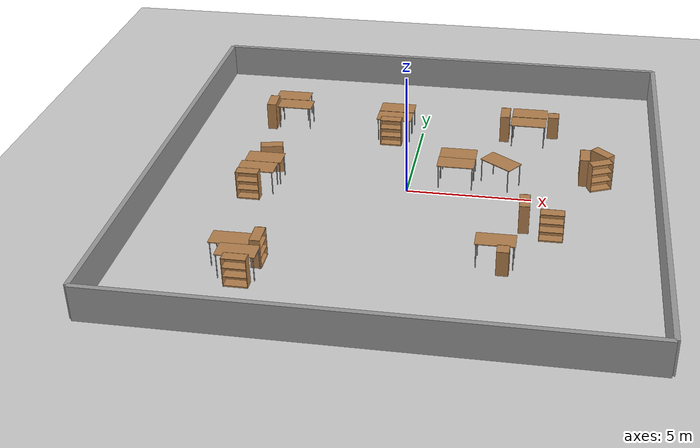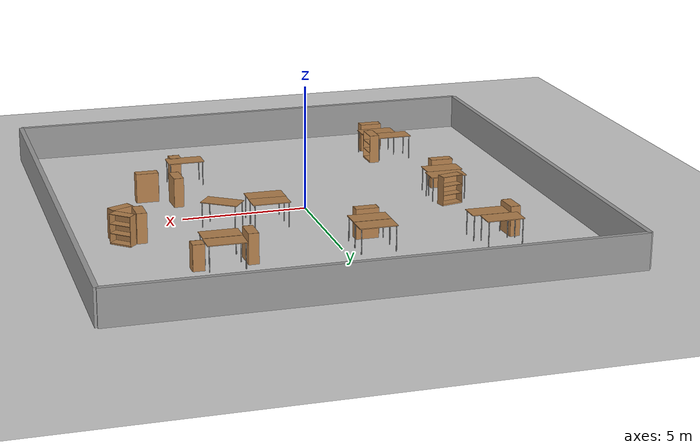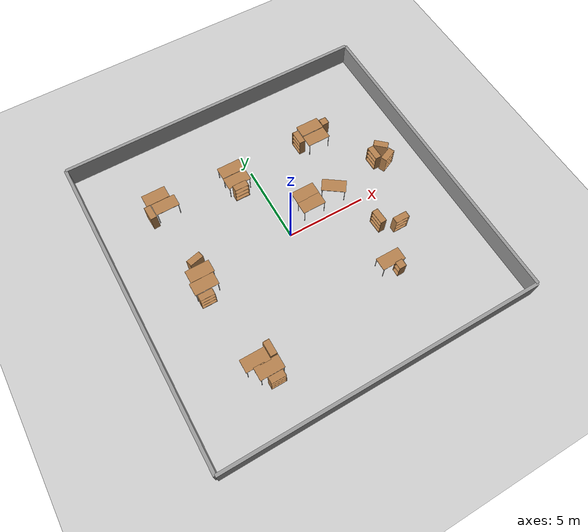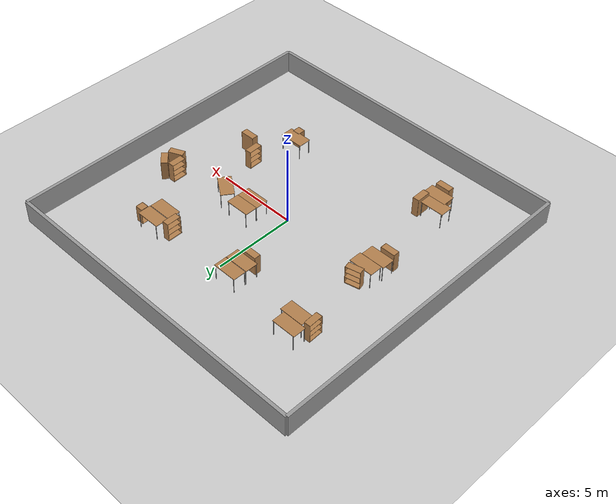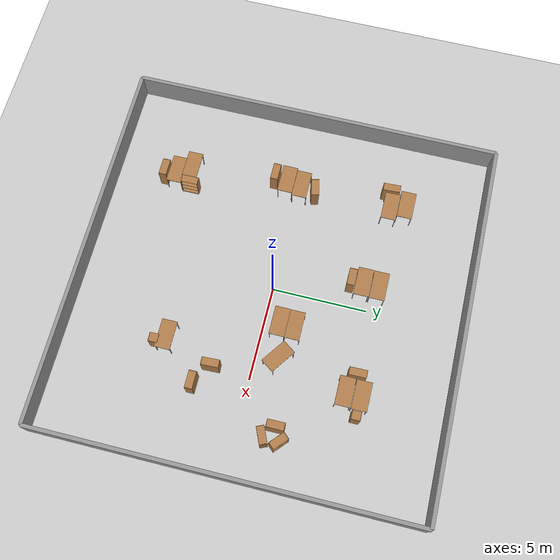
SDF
<sdf version="1.6">
 <world name="default">
  <light name="sun" type="directional">
   <cast_shadows>0</cast_shadows>
   <pose>0 0 10 0 -0 0</pose>
   <diffuse>0.8 0.8 0.8 1</diffuse>
   <specular>0.1 0.1 0.1 1</specular>
   <attenuation>
    <range>1000</range>
    <constant>0.9</constant>
    <linear>0.01</linear>
    <quadratic>0.001</quadratic>
   </attenuation>
   <direction>-0.5 0.5 -1</direction>
  </light>
  <model name="ground_plane">
   <static>1</static>
   <link name="link">
    <collision name="collision">
     <geometry><plane><normal>0 0 1</normal><size>100 100</size></plane></geometry>
     <surface><friction><ode><mu>100</mu><mu2>50</mu2></ode></friction></surface>
    </collision>
    <visual name="visual">
     <cast_shadows>0</cast_shadows>
     <geometry><plane><normal>0 0 1</normal><size>100 100</size></plane></geometry>
     <material>
      <script><uri>file://media/materials/scripts/gazebo.material</uri><name>Gazebo/Grey</name></script>
     </material>
    </visual>
   </link>
  </model>
  <gravity>0 0 -9.8</gravity>
  <magnetic_field>6e-06 2.3e-05 -4.2e-05</magnetic_field>
  <atmosphere type="adiabatic"/>
  <physics name="default_physics" default="0" type="ode">
   <max_step_size>0.001</max_step_size>
   <real_time_factor>1</real_time_factor>
   <real_time_update_rate>1000</real_time_update_rate>
  </physics>
  <scene><ambient>0.4 0.4 0.4 1</ambient><background>0.7 0.7 0.7 1</background><shadows>1</shadows></scene>
  <spherical_coordinates>
   <surface_model>EARTH_WGS84</surface_model>
   <latitude_deg>0</latitude_deg>
   <longitude_deg>0</longitude_deg>
   <elevation>0</elevation>
   <heading_deg>0</heading_deg>
  </spherical_coordinates>
  <model name="grey_wall_1">
   <link name="link">
    <inertial>
     <mass>1</mass>
     <inertia><ixx>1</ixx><ixy>0</ixy><ixz>0</ixz><iyy>1</iyy><iyz>0</iyz><izz>1</izz></inertia>
    </inertial>
    <visual name="visual">
     <cast_shadows>0</cast_shadows>
     <geometry><box><size>20 0.2 2.8</size></box></geometry>
     <material>
      <script>
       <uri>model://grey_wall/materials/scripts</uri>
       <uri>model://grey_wall/materials/textures</uri>
       <name>vrc/grey_wall</name>
      </script>
      <ambient>1 1 1 1</ambient>
      <diffuse>1 1 1 1</diffuse>
      <specular>0 0 0 1</specular>
      <emissive>0 0 0 1</emissive>
      <shader type="vertex"><normal_map>__default__</normal_map></shader>
     </material>
    </visual>
    <collision name="collision">
     <geometry><box><size>20 0.2 2.8</size></box></geometry>
     <surface>
      <friction>
       <ode><mu>1</mu><mu2>1</mu2><fdir1>0 0 0</fdir1><slip1>0</slip1><slip2>0</slip2></ode>
       <torsional>
        <coefficient>1</coefficient>
        <patch_radius>0</patch_radius>
        <surface_radius>0</surface_radius>
        <use_patch_radius>1</use_patch_radius>
        <ode><slip>0</slip></ode>
       </torsional>
      </friction>
      <bounce><restitution_coefficient>0</restitution_coefficient><threshold>1e+06</threshold></bounce>
      <contact>
       <collide_without_contact>0</collide_without_contact>
       <collide_without_contact_bitmask>1</collide_without_contact_bitmask>
       <collide_bitmask>1</collide_bitmask>
       <ode>
        <soft_cfm>0</soft_cfm>
        <soft_erp>0.2</soft_erp>
        <kp>1e+13</kp>
        <kd>1</kd>
        <max_vel>0.01</max_vel>
        <min_depth>0</min_depth>
       </ode>
       <bullet>
        <split_impulse>1</split_impulse>
        <split_impulse_penetration_threshold>-0.01</split_impulse_penetration_threshold>
        <soft_cfm>0</soft_cfm>
        <soft_erp>0.2</soft_erp>
        <kp>1e+13</kp>
        <kd>1</kd>
       </bullet>
      </contact>
     </surface>
    </collision>
   </link>
   <static>1</static>
   <pose>0 10 0 0 -0 0</pose>
  </model>
  <model name="grey_wall_2">
   <link name="link">
    <inertial>
     <mass>1</mass>
     <inertia><ixx>1</ixx><ixy>0</ixy><ixz>0</ixz><iyy>1</iyy><iyz>0</iyz><izz>1</izz></inertia>
    </inertial>
    <visual name="visual">
     <cast_shadows>0</cast_shadows>
     <geometry><box><size>20 0.2 2.8</size></box></geometry>
     <material>
      <script>
       <uri>model://grey_wall/materials/scripts</uri>
       <uri>model://grey_wall/materials/textures</uri>
       <name>vrc/grey_wall</name>
      </script>
      <ambient>1 1 1 1</ambient>
      <diffuse>1 1 1 1</diffuse>
      <specular>0 0 0 1</specular>
      <emissive>0 0 0 1</emissive>
      <shader type="vertex"><normal_map>__default__</normal_map></shader>
     </material>
    </visual>
    <collision name="collision">
     <geometry><box><size>20 0.2 2.8</size></box></geometry>
     <surface>
      <friction>
       <ode><mu>1</mu><mu2>1</mu2><fdir1>0 0 0</fdir1><slip1>0</slip1><slip2>0</slip2></ode>
       <torsional>
        <coefficient>1</coefficient>
        <patch_radius>0</patch_radius>
        <surface_radius>0</surface_radius>
        <use_patch_radius>1</use_patch_radius>
        <ode><slip>0</slip></ode>
       </torsional>
      </friction>
      <bounce><restitution_coefficient>0</restitution_coefficient><threshold>1e+06</threshold></bounce>
      <contact>
       <collide_without_contact>0</collide_without_contact>
       <collide_without_contact_bitmask>1</collide_without_contact_bitmask>
       <collide_bitmask>1</collide_bitmask>
       <ode>
        <soft_cfm>0</soft_cfm>
        <soft_erp>0.2</soft_erp>
        <kp>1e+13</kp>
        <kd>1</kd>
        <max_vel>0.01</max_vel>
        <min_depth>0</min_depth>
       </ode>
       <bullet>
        <split_impulse>1</split_impulse>
        <split_impulse_penetration_threshold>-0.01</split_impulse_penetration_threshold>
        <soft_cfm>0</soft_cfm>
        <soft_erp>0.2</soft_erp>
        <kp>1e+13</kp>
        <kd>1</kd>
       </bullet>
      </contact>
     </surface>
    </collision>
   </link>
   <static>1</static>
   <pose>0 -10 0 0 -0 0</pose>
  </model>
  <model name="grey_wall_3">
   <link name="link">
    <inertial>
     <mass>1</mass>
     <inertia><ixx>1</ixx><ixy>0</ixy><ixz>0</ixz><iyy>1</iyy><iyz>0</iyz><izz>1</izz></inertia>
    </inertial>
    <visual name="visual">
     <cast_shadows>0</cast_shadows>
     <geometry><box><size>20 0.2 2.8</size></box></geometry>
     <material>
      <script>
       <uri>model://grey_wall/materials/scripts</uri>
       <uri>model://grey_wall/materials/textures</uri>
       <name>vrc/grey_wall</name>
      </script>
      <ambient>1 1 1 1</ambient>
      <diffuse>1 1 1 1</diffuse>
      <specular>0 0 0 1</specular>
      <emissive>0 0 0 1</emissive>
      <shader type="vertex"><normal_map>__default__</normal_map></shader>
     </material>
    </visual>
    <collision name="collision">
     <geometry><box><size>20 0.2 2.8</size></box></geometry>
     <surface>
      <friction>
       <ode><mu>1</mu><mu2>1</mu2><fdir1>0 0 0</fdir1><slip1>0</slip1><slip2>0</slip2></ode>
       <torsional>
        <coefficient>1</coefficient>
        <patch_radius>0</patch_radius>
        <surface_radius>0</surface_radius>
        <use_patch_radius>1</use_patch_radius>
        <ode><slip>0</slip></ode>
       </torsional>
      </friction>
      <bounce><restitution_coefficient>0</restitution_coefficient><threshold>1e+06</threshold></bounce>
      <contact>
       <collide_without_contact>0</collide_without_contact>
       <collide_without_contact_bitmask>1</collide_without_contact_bitmask>
       <collide_bitmask>1</collide_bitmask>
       <ode>
        <soft_cfm>0</soft_cfm>
        <soft_erp>0.2</soft_erp>
        <kp>1e+13</kp>
        <kd>1</kd>
        <max_vel>0.01</max_vel>
        <min_depth>0</min_depth>
       </ode>
       <bullet>
        <split_impulse>1</split_impulse>
        <split_impulse_penetration_threshold>-0.01</split_impulse_penetration_threshold>
        <soft_cfm>0</soft_cfm>
        <soft_erp>0.2</soft_erp>
        <kp>1e+13</kp>
        <kd>1</kd>
       </bullet>
      </contact>
     </surface>
    </collision>
   </link>
   <static>1</static>
   <pose>-10 0 0 0 0 -1.5708</pose>
  </model>
  <model name="grey_wall_4">
   <link name="link">
    <inertial>
     <mass>1</mass>
     <inertia><ixx>1</ixx><ixy>0</ixy><ixz>0</ixz><iyy>1</iyy><iyz>0</iyz><izz>1</izz></inertia>
    </inertial>
    <visual name="visual">
     <cast_shadows>0</cast_shadows>
     <geometry><box><size>20 0.2 2.8</size></box></geometry>
     <material>
      <script>
       <uri>model://grey_wall/materials/scripts</uri>
       <uri>model://grey_wall/materials/textures</uri>
       <name>vrc/grey_wall</name>
      </script>
      <ambient>1 1 1 1</ambient>
      <diffuse>1 1 1 1</diffuse>
      <specular>0 0 0 1</specular>
      <emissive>0 0 0 1</emissive>
      <shader type="vertex"><normal_map>__default__</normal_map></shader>
     </material>
    </visual>
    <collision name="collision">
     <geometry><box><size>20 0.2 2.8</size></box></geometry>
     <surface>
      <friction>
       <ode><mu>1</mu><mu2>1</mu2><fdir1>0 0 0</fdir1><slip1>0</slip1><slip2>0</slip2></ode>
       <torsional>
        <coefficient>1</coefficient>
        <patch_radius>0</patch_radius>
        <surface_radius>0</surface_radius>
        <use_patch_radius>1</use_patch_radius>
        <ode><slip>0</slip></ode>
       </torsional>
      </friction>
      <bounce><restitution_coefficient>0</restitution_coefficient><threshold>1e+06</threshold></bounce>
      <contact>
       <collide_without_contact>0</collide_without_contact>
       <collide_without_contact_bitmask>1</collide_without_contact_bitmask>
       <collide_bitmask>1</collide_bitmask>
       <ode>
        <soft_cfm>0</soft_cfm>
        <soft_erp>0.2</soft_erp>
        <kp>1e+13</kp>
        <kd>1</kd>
        <max_vel>0.01</max_vel>
        <min_depth>0</min_depth>
       </ode>
       <bullet>
        <split_impulse>1</split_impulse>
        <split_impulse_penetration_threshold>-0.01</split_impulse_penetration_threshold>
        <soft_cfm>0</soft_cfm>
        <soft_erp>0.2</soft_erp>
        <kp>1e+13</kp>
        <kd>1</kd>
       </bullet>
      </contact>
     </surface>
    </collision>
   </link>
   <static>1</static>
   <pose>10 0 0 0 -0 1.5708</pose>
  </model>
  <model name="cabinet">
   <static>1</static>
   <link name="cabinet_bottom_plate">
    <inertial>
     <pose>0 0 -1 0 -0 0</pose>
     <inertia><ixx>2.05</ixx><ixy>0</ixy><ixz>0</ixz><iyy>2.05</iyy><iyz>0</iyz><izz>2.05</izz></inertia>
     <mass>25</mass>
    </inertial>
    <collision name="cabinet_bottom_plate_geom">
     <pose>0 0 0.01 0 -0 0</pose>
     <geometry><box><size>0.45 0.45 0.02</size></box></geometry>
    </collision>
    <visual name="cabinet_bottom_plate_geom_visual">
     <pose>0 0 0.01 0 -0 0</pose>
     <geometry><box><size>0.45 0.45 0.02</size></box></geometry>
     <material>
      <script><uri>file://media/materials/scripts/gazebo.material</uri><name>Gazebo/Wood</name></script>
     </material>
    </visual>
    <collision name="cabinet_bottom_plate_geom_cabinet_back_plate">
     <pose>0.235 0 0.51 0 -0 0</pose>
     <geometry><box><size>0.02 0.45 1.02</size></box></geometry>
    </collision>
    <visual name="cabinet_bottom_plate_geom_cabinet_back_plate_visual">
     <pose>0.235 0 0.51 0 -0 0</pose>
     <geometry><box><size>0.02 0.45 1.02</size></box></geometry>
     <material>
      <script><uri>file://media/materials/scripts/gazebo.material</uri><name>Gazebo/Wood</name></script>
     </material>
    </visual>
    <collision name="cabinet_bottom_plate_geom_cabinet_left_plate">
     <pose>0 0.235 0.51 0 -0 0</pose>
     <geometry><box><size>0.45 0.02 1.02</size></box></geometry>
    </collision>
    <visual name="cabinet_bottom_plate_geom_cabinet_left_plate_visual">
     <pose>0 0.235 0.51 0 -0 0</pose>
     <geometry><box><size>0.45 0.02 1.02</size></box></geometry>
     <material>
      <script><uri>file://media/materials/scripts/gazebo.material</uri><name>Gazebo/Wood</name></script>
     </material>
    </visual>
    <collision name="cabinet_bottom_plate_geom_cabinet_middle_plate">
     <pose>0 0 0.51 0 -0 0</pose>
     <geometry><box><size>0.45 0.45 0.02</size></box></geometry>
    </collision>
    <visual name="cabinet_bottom_plate_geom_cabinet_middle_plate_visual">
     <pose>0 0 0.51 0 -0 0</pose>
     <geometry><box><size>0.45 0.45 0.02</size></box></geometry>
     <material>
      <script><uri>file://media/materials/scripts/gazebo.material</uri><name>Gazebo/Wood</name></script>
     </material>
    </visual>
    <collision name="cabinet_bottom_plate_geom_cabinet_right_plate">
     <pose>0 -0.235 0.51 0 -0 0</pose>
     <geometry><box><size>0.45 0.02 1.02</size></box></geometry>
    </collision>
    <visual name="cabinet_bottom_plate_geom_cabinet_right_plate_visual">
     <pose>0 -0.235 0.51 0 -0 0</pose>
     <geometry><box><size>0.45 0.02 1.02</size></box></geometry>
     <material>
      <script><uri>file://media/materials/scripts/gazebo.material</uri><name>Gazebo/Wood</name></script>
     </material>
    </visual>
    <collision name="cabinet_bottom_plate_geom_cabinet_top_plate">
     <pose>0 0 1.01 0 -0 0</pose>
     <geometry><box><size>0.45 0.45 0.02</size></box></geometry>
    </collision>
    <visual name="cabinet_bottom_plate_geom_cabinet_top_plate_visual">
     <pose>0 0 1.01 0 -0 0</pose>
     <geometry><box><size>0.45 0.45 0.02</size></box></geometry>
     <material>
      <script><uri>file://media/materials/scripts/gazebo.material</uri><name>Gazebo/Wood</name></script>
     </material>
    </visual>
   </link>
   <pose>4.23229 -5.13046 0 0 -0 0</pose>
  </model>
  <model name="bookshelf">
   <static>1</static>
   <link name="link">
    <inertial><mass>1</mass></inertial>
    <collision name="back">
     <pose>0 0.005 0.6 0 -0 0</pose>
     <geometry><box><size>0.9 0.01 1.2</size></box></geometry>
    </collision>
    <visual name="visual1">
     <pose>0 0.005 0.6 0 -0 0</pose>
     <geometry><box><size>0.9 0.01 1.2</size></box></geometry>
     <material>
      <script><uri>file://media/materials/scripts/gazebo.material</uri><name>Gazebo/Wood</name></script>
     </material>
    </visual>
    <collision name="left_side">
     <pose>0.45 -0.195 0.6 0 -0 0</pose>
     <geometry><box><size>0.02 0.4 1.2</size></box></geometry>
    </collision>
    <visual name="visual2">
     <pose>0.45 -0.195 0.6 0 -0 0</pose>
     <geometry><box><size>0.02 0.4 1.2</size></box></geometry>
     <material>
      <script><uri>file://media/materials/scripts/gazebo.material</uri><name>Gazebo/Wood</name></script>
     </material>
    </visual>
    <collision name="right_side">
     <pose>-0.45 -0.195 0.6 0 -0 0</pose>
     <geometry><box><size>0.02 0.4 1.2</size></box></geometry>
    </collision>
    <visual name="visual3">
     <pose>-0.45 -0.195 0.6 0 -0 0</pose>
     <geometry><box><size>0.02 0.4 1.2</size></box></geometry>
     <material>
      <script><uri>file://media/materials/scripts/gazebo.material</uri><name>Gazebo/Wood</name></script>
     </material>
    </visual>
    <collision name="bottom">
     <pose>0 -0.195 0.03 0 -0 0</pose>
     <geometry><box><size>0.88 0.4 0.06</size></box></geometry>
    </collision>
    <visual name="visual4">
     <pose>0 -0.195 0.03 0 -0 0</pose>
     <geometry><box><size>0.88 0.4 0.06</size></box></geometry>
     <material>
      <script><uri>file://media/materials/scripts/gazebo.material</uri><name>Gazebo/Wood</name></script>
     </material>
    </visual>
    <collision name="top">
     <pose>0 -0.195 1.19 0 -0 0</pose>
     <geometry><box><size>0.88 0.4 0.02</size></box></geometry>
    </collision>
    <visual name="visual5">
     <pose>0 -0.195 1.19 0 -0 0</pose>
     <geometry><box><size>0.88 0.4 0.02</size></box></geometry>
     <material>
      <script><uri>file://media/materials/scripts/gazebo.material</uri><name>Gazebo/Wood</name></script>
     </material>
    </visual>
    <collision name="low_shelf">
     <pose>0 -0.195 0.43 0 -0 0</pose>
     <geometry><box><size>0.88 0.4 0.02</size></box></geometry>
    </collision>
    <visual name="visual6">
     <pose>0 -0.195 0.43 0 -0 0</pose>
     <geometry><box><size>0.88 0.4 0.02</size></box></geometry>
     <material>
      <script><uri>file://media/materials/scripts/gazebo.material</uri><name>Gazebo/Wood</name></script>
     </material>
    </visual>
    <collision name="high_shelf">
     <pose>0 -0.195 0.8 0 -0 0</pose>
     <geometry><box><size>0.88 0.4 0.02</size></box></geometry>
    </collision>
    <visual name="visual7">
     <pose>0 -0.195 0.8 0 -0 0</pose>
     <geometry><box><size>0.88 0.4 0.02</size></box></geometry>
     <material>
      <script><uri>file://media/materials/scripts/gazebo.material</uri><name>Gazebo/Wood</name></script>
     </material>
    </visual>
   </link>
   <pose>5.88793 -2.5165 0 0 -0 0</pose>
  </model>
  <model name="bookshelf_0">
   <static>1</static>
   <link name="link">
    <inertial><mass>1</mass></inertial>
    <collision name="back">
     <pose>0 0.005 0.6 0 -0 0</pose>
     <geometry><box><size>0.9 0.01 1.2</size></box></geometry>
    </collision>
    <visual name="visual1">
     <pose>0 0.005 0.6 0 -0 0</pose>
     <geometry><box><size>0.9 0.01 1.2</size></box></geometry>
     <material>
      <script><uri>file://media/materials/scripts/gazebo.material</uri><name>Gazebo/Wood</name></script>
     </material>
    </visual>
    <collision name="left_side">
     <pose>0.45 -0.195 0.6 0 -0 0</pose>
     <geometry><box><size>0.02 0.4 1.2</size></box></geometry>
    </collision>
    <visual name="visual2">
     <pose>0.45 -0.195 0.6 0 -0 0</pose>
     <geometry><box><size>0.02 0.4 1.2</size></box></geometry>
     <material>
      <script><uri>file://media/materials/scripts/gazebo.material</uri><name>Gazebo/Wood</name></script>
     </material>
    </visual>
    <collision name="right_side">
     <pose>-0.45 -0.195 0.6 0 -0 0</pose>
     <geometry><box><size>0.02 0.4 1.2</size></box></geometry>
    </collision>
    <visual name="visual3">
     <pose>-0.45 -0.195 0.6 0 -0 0</pose>
     <geometry><box><size>0.02 0.4 1.2</size></box></geometry>
     <material>
      <script><uri>file://media/materials/scripts/gazebo.material</uri><name>Gazebo/Wood</name></script>
     </material>
    </visual>
    <collision name="bottom">
     <pose>0 -0.195 0.03 0 -0 0</pose>
     <geometry><box><size>0.88 0.4 0.06</size></box></geometry>
    </collision>
    <visual name="visual4">
     <pose>0 -0.195 0.03 0 -0 0</pose>
     <geometry><box><size>0.88 0.4 0.06</size></box></geometry>
     <material>
      <script><uri>file://media/materials/scripts/gazebo.material</uri><name>Gazebo/Wood</name></script>
     </material>
    </visual>
    <collision name="top">
     <pose>0 -0.195 1.19 0 -0 0</pose>
     <geometry><box><size>0.88 0.4 0.02</size></box></geometry>
    </collision>
    <visual name="visual5">
     <pose>0 -0.195 1.19 0 -0 0</pose>
     <geometry><box><size>0.88 0.4 0.02</size></box></geometry>
     <material>
      <script><uri>file://media/materials/scripts/gazebo.material</uri><name>Gazebo/Wood</name></script>
     </material>
    </visual>
    <collision name="low_shelf">
     <pose>0 -0.195 0.43 0 -0 0</pose>
     <geometry><box><size>0.88 0.4 0.02</size></box></geometry>
    </collision>
    <visual name="visual6">
     <pose>0 -0.195 0.43 0 -0 0</pose>
     <geometry><box><size>0.88 0.4 0.02</size></box></geometry>
     <material>
      <script><uri>file://media/materials/scripts/gazebo.material</uri><name>Gazebo/Wood</name></script>
     </material>
    </visual>
    <collision name="high_shelf">
     <pose>0 -0.195 0.8 0 -0 0</pose>
     <geometry><box><size>0.88 0.4 0.02</size></box></geometry>
    </collision>
    <visual name="visual7">
     <pose>0 -0.195 0.8 0 -0 0</pose>
     <geometry><box><size>0.88 0.4 0.02</size></box></geometry>
     <material>
      <script><uri>file://media/materials/scripts/gazebo.material</uri><name>Gazebo/Wood</name></script>
     </material>
    </visual>
   </link>
   <pose>7.61248 2.05887 0 0 -0 2.40643</pose>
  </model>
  <model name="table">
   <static>1</static>
   <link name="link">
    <collision name="surface">
     <pose>0 0 1 0 -0 0</pose>
     <geometry><box><size>1.5 0.8 0.03</size></box></geometry>
     <surface><friction><ode><mu>0.6</mu><mu2>0.6</mu2></ode></friction></surface>
    </collision>
    <visual name="visual1">
     <pose>0 0 1 0 -0 0</pose>
     <geometry><box><size>1.5 0.8 0.03</size></box></geometry>
     <material>
      <script><uri>file://media/materials/scripts/gazebo.material</uri><name>Gazebo/Wood</name></script>
     </material>
    </visual>
    <collision name="front_left_leg">
     <pose>0.68 0.38 0.5 0 -0 0</pose>
     <geometry><cylinder><radius>0.02</radius><length>1</length></cylinder></geometry>
    </collision>
    <visual name="front_left_leg">
     <pose>0.68 0.38 0.5 0 -0 0</pose>
     <geometry><cylinder><radius>0.02</radius><length>1</length></cylinder></geometry>
     <material>
      <script><uri>file://media/materials/scripts/gazebo.material</uri><name>Gazebo/Grey</name></script>
     </material>
    </visual>
    <collision name="front_right_leg">
     <pose>0.68 -0.38 0.5 0 -0 0</pose>
     <geometry><cylinder><radius>0.02</radius><length>1</length></cylinder></geometry>
    </collision>
    <visual name="front_right_leg">
     <pose>0.68 -0.38 0.5 0 -0 0</pose>
     <geometry><cylinder><radius>0.02</radius><length>1</length></cylinder></geometry>
     <material>
      <script><uri>file://media/materials/scripts/gazebo.material</uri><name>Gazebo/Grey</name></script>
     </material>
    </visual>
    <collision name="back_right_leg">
     <pose>-0.68 -0.38 0.5 0 -0 0</pose>
     <geometry><cylinder><radius>0.02</radius><length>1</length></cylinder></geometry>
    </collision>
    <visual name="back_right_leg">
     <pose>-0.68 -0.38 0.5 0 -0 0</pose>
     <geometry><cylinder><radius>0.02</radius><length>1</length></cylinder></geometry>
     <material>
      <script><uri>file://media/materials/scripts/gazebo.material</uri><name>Gazebo/Grey</name></script>
     </material>
    </visual>
    <collision name="back_left_leg">
     <pose>-0.68 0.38 0.5 0 -0 0</pose>
     <geometry><cylinder><radius>0.02</radius><length>1</length></cylinder></geometry>
    </collision>
    <visual name="back_left_leg">
     <pose>-0.68 0.38 0.5 0 -0 0</pose>
     <geometry><cylinder><radius>0.02</radius><length>1</length></cylinder></geometry>
     <material>
      <script><uri>file://media/materials/scripts/gazebo.material</uri><name>Gazebo/Grey</name></script>
     </material>
    </visual>
   </link>
   <pose>3.67725 1.1887 0 0 0 -0.613987</pose>
  </model>
  <model name="table_0">
   <static>1</static>
   <link name="link">
    <collision name="surface">
     <pose>0 0 1 0 -0 0</pose>
     <geometry><box><size>1.5 0.8 0.03</size></box></geometry>
     <surface><friction><ode><mu>0.6</mu><mu2>0.6</mu2></ode></friction></surface>
    </collision>
    <visual name="visual1">
     <pose>0 0 1 0 -0 0</pose>
     <geometry><box><size>1.5 0.8 0.03</size></box></geometry>
     <material>
      <script><uri>file://media/materials/scripts/gazebo.material</uri><name>Gazebo/Wood</name></script>
     </material>
    </visual>
    <collision name="front_left_leg">
     <pose>0.68 0.38 0.5 0 -0 0</pose>
     <geometry><cylinder><radius>0.02</radius><length>1</length></cylinder></geometry>
    </collision>
    <visual name="front_left_leg">
     <pose>0.68 0.38 0.5 0 -0 0</pose>
     <geometry><cylinder><radius>0.02</radius><length>1</length></cylinder></geometry>
     <material>
      <script><uri>file://media/materials/scripts/gazebo.material</uri><name>Gazebo/Grey</name></script>
     </material>
    </visual>
    <collision name="front_right_leg">
     <pose>0.68 -0.38 0.5 0 -0 0</pose>
     <geometry><cylinder><radius>0.02</radius><length>1</length></cylinder></geometry>
    </collision>
    <visual name="front_right_leg">
     <pose>0.68 -0.38 0.5 0 -0 0</pose>
     <geometry><cylinder><radius>0.02</radius><length>1</length></cylinder></geometry>
     <material>
      <script><uri>file://media/materials/scripts/gazebo.material</uri><name>Gazebo/Grey</name></script>
     </material>
    </visual>
    <collision name="back_right_leg">
     <pose>-0.68 -0.38 0.5 0 -0 0</pose>
     <geometry><cylinder><radius>0.02</radius><length>1</length></cylinder></geometry>
    </collision>
    <visual name="back_right_leg">
     <pose>-0.68 -0.38 0.5 0 -0 0</pose>
     <geometry><cylinder><radius>0.02</radius><length>1</length></cylinder></geometry>
     <material>
      <script><uri>file://media/materials/scripts/gazebo.material</uri><name>Gazebo/Grey</name></script>
     </material>
    </visual>
    <collision name="back_left_leg">
     <pose>-0.68 0.38 0.5 0 -0 0</pose>
     <geometry><cylinder><radius>0.02</radius><length>1</length></cylinder></geometry>
    </collision>
    <visual name="back_left_leg">
     <pose>-0.68 0.38 0.5 0 -0 0</pose>
     <geometry><cylinder><radius>0.02</radius><length>1</length></cylinder></geometry>
     <material>
      <script><uri>file://media/materials/scripts/gazebo.material</uri><name>Gazebo/Grey</name></script>
     </material>
    </visual>
   </link>
   <pose>-1.18424 5.36108 0 0 -0 0</pose>
  </model>
  <model name="table_1">
   <static>1</static>
   <link name="link">
    <collision name="surface">
     <pose>0 0 1 0 -0 0</pose>
     <geometry><box><size>1.5 0.8 0.03</size></box></geometry>
     <surface><friction><ode><mu>0.6</mu><mu2>0.6</mu2></ode></friction></surface>
    </collision>
    <visual name="visual1">
     <pose>0 0 1 0 -0 0</pose>
     <geometry><box><size>1.5 0.8 0.03</size></box></geometry>
     <material>
      <script><uri>file://media/materials/scripts/gazebo.material</uri><name>Gazebo/Wood</name></script>
     </material>
    </visual>
    <collision name="front_left_leg">
     <pose>0.68 0.38 0.5 0 -0 0</pose>
     <geometry><cylinder><radius>0.02</radius><length>1</length></cylinder></geometry>
    </collision>
    <visual name="front_left_leg">
     <pose>0.68 0.38 0.5 0 -0 0</pose>
     <geometry><cylinder><radius>0.02</radius><length>1</length></cylinder></geometry>
     <material>
      <script><uri>file://media/materials/scripts/gazebo.material</uri><name>Gazebo/Grey</name></script>
     </material>
    </visual>
    <collision name="front_right_leg">
     <pose>0.68 -0.38 0.5 0 -0 0</pose>
     <geometry><cylinder><radius>0.02</radius><length>1</length></cylinder></geometry>
    </collision>
    <visual name="front_right_leg">
     <pose>0.68 -0.38 0.5 0 -0 0</pose>
     <geometry><cylinder><radius>0.02</radius><length>1</length></cylinder></geometry>
     <material>
      <script><uri>file://media/materials/scripts/gazebo.material</uri><name>Gazebo/Grey</name></script>
     </material>
    </visual>
    <collision name="back_right_leg">
     <pose>-0.68 -0.38 0.5 0 -0 0</pose>
     <geometry><cylinder><radius>0.02</radius><length>1</length></cylinder></geometry>
    </collision>
    <visual name="back_right_leg">
     <pose>-0.68 -0.38 0.5 0 -0 0</pose>
     <geometry><cylinder><radius>0.02</radius><length>1</length></cylinder></geometry>
     <material>
      <script><uri>file://media/materials/scripts/gazebo.material</uri><name>Gazebo/Grey</name></script>
     </material>
    </visual>
    <collision name="back_left_leg">
     <pose>-0.68 0.38 0.5 0 -0 0</pose>
     <geometry><cylinder><radius>0.02</radius><length>1</length></cylinder></geometry>
    </collision>
    <visual name="back_left_leg">
     <pose>-0.68 0.38 0.5 0 -0 0</pose>
     <geometry><cylinder><radius>0.02</radius><length>1</length></cylinder></geometry>
     <material>
      <script><uri>file://media/materials/scripts/gazebo.material</uri><name>Gazebo/Grey</name></script>
     </material>
    </visual>
   </link>
   <pose>-1.19395 4.53347 0 0 -0 0</pose>
  </model>
  <model name="table_2">
   <static>1</static>
   <link name="link">
    <collision name="surface">
     <pose>0 0 1 0 -0 0</pose>
     <geometry><box><size>1.5 0.8 0.03</size></box></geometry>
     <surface><friction><ode><mu>0.6</mu><mu2>0.6</mu2></ode></friction></surface>
    </collision>
    <visual name="visual1">
     <pose>0 0 1 0 -0 0</pose>
     <geometry><box><size>1.5 0.8 0.03</size></box></geometry>
     <material>
      <script><uri>file://media/materials/scripts/gazebo.material</uri><name>Gazebo/Wood</name></script>
     </material>
    </visual>
    <collision name="front_left_leg">
     <pose>0.68 0.38 0.5 0 -0 0</pose>
     <geometry><cylinder><radius>0.02</radius><length>1</length></cylinder></geometry>
    </collision>
    <visual name="front_left_leg">
     <pose>0.68 0.38 0.5 0 -0 0</pose>
     <geometry><cylinder><radius>0.02</radius><length>1</length></cylinder></geometry>
     <material>
      <script><uri>file://media/materials/scripts/gazebo.material</uri><name>Gazebo/Grey</name></script>
     </material>
    </visual>
    <collision name="front_right_leg">
     <pose>0.68 -0.38 0.5 0 -0 0</pose>
     <geometry><cylinder><radius>0.02</radius><length>1</length></cylinder></geometry>
    </collision>
    <visual name="front_right_leg">
     <pose>0.68 -0.38 0.5 0 -0 0</pose>
     <geometry><cylinder><radius>0.02</radius><length>1</length></cylinder></geometry>
     <material>
      <script><uri>file://media/materials/scripts/gazebo.material</uri><name>Gazebo/Grey</name></script>
     </material>
    </visual>
    <collision name="back_right_leg">
     <pose>-0.68 -0.38 0.5 0 -0 0</pose>
     <geometry><cylinder><radius>0.02</radius><length>1</length></cylinder></geometry>
    </collision>
    <visual name="back_right_leg">
     <pose>-0.68 -0.38 0.5 0 -0 0</pose>
     <geometry><cylinder><radius>0.02</radius><length>1</length></cylinder></geometry>
     <material>
      <script><uri>file://media/materials/scripts/gazebo.material</uri><name>Gazebo/Grey</name></script>
     </material>
    </visual>
    <collision name="back_left_leg">
     <pose>-0.68 0.38 0.5 0 -0 0</pose>
     <geometry><cylinder><radius>0.02</radius><length>1</length></cylinder></geometry>
    </collision>
    <visual name="back_left_leg">
     <pose>-0.68 0.38 0.5 0 -0 0</pose>
     <geometry><cylinder><radius>0.02</radius><length>1</length></cylinder></geometry>
     <material>
      <script><uri>file://media/materials/scripts/gazebo.material</uri><name>Gazebo/Grey</name></script>
     </material>
    </visual>
   </link>
   <pose>4.61816 5.644 0 0 -0 0</pose>
  </model>
  <model name="table_3">
   <static>1</static>
   <link name="link">
    <collision name="surface">
     <pose>0 0 1 0 -0 0</pose>
     <geometry><box><size>1.5 0.8 0.03</size></box></geometry>
     <surface><friction><ode><mu>0.6</mu><mu2>0.6</mu2></ode></friction></surface>
    </collision>
    <visual name="visual1">
     <pose>0 0 1 0 -0 0</pose>
     <geometry><box><size>1.5 0.8 0.03</size></box></geometry>
     <material>
      <script><uri>file://media/materials/scripts/gazebo.material</uri><name>Gazebo/Wood</name></script>
     </material>
    </visual>
    <collision name="front_left_leg">
     <pose>0.68 0.38 0.5 0 -0 0</pose>
     <geometry><cylinder><radius>0.02</radius><length>1</length></cylinder></geometry>
    </collision>
    <visual name="front_left_leg">
     <pose>0.68 0.38 0.5 0 -0 0</pose>
     <geometry><cylinder><radius>0.02</radius><length>1</length></cylinder></geometry>
     <material>
      <script><uri>file://media/materials/scripts/gazebo.material</uri><name>Gazebo/Grey</name></script>
     </material>
    </visual>
    <collision name="front_right_leg">
     <pose>0.68 -0.38 0.5 0 -0 0</pose>
     <geometry><cylinder><radius>0.02</radius><length>1</length></cylinder></geometry>
    </collision>
    <visual name="front_right_leg">
     <pose>0.68 -0.38 0.5 0 -0 0</pose>
     <geometry><cylinder><radius>0.02</radius><length>1</length></cylinder></geometry>
     <material>
      <script><uri>file://media/materials/scripts/gazebo.material</uri><name>Gazebo/Grey</name></script>
     </material>
    </visual>
    <collision name="back_right_leg">
     <pose>-0.68 -0.38 0.5 0 -0 0</pose>
     <geometry><cylinder><radius>0.02</radius><length>1</length></cylinder></geometry>
    </collision>
    <visual name="back_right_leg">
     <pose>-0.68 -0.38 0.5 0 -0 0</pose>
     <geometry><cylinder><radius>0.02</radius><length>1</length></cylinder></geometry>
     <material>
      <script><uri>file://media/materials/scripts/gazebo.material</uri><name>Gazebo/Grey</name></script>
     </material>
    </visual>
    <collision name="back_left_leg">
     <pose>-0.68 0.38 0.5 0 -0 0</pose>
     <geometry><cylinder><radius>0.02</radius><length>1</length></cylinder></geometry>
    </collision>
    <visual name="back_left_leg">
     <pose>-0.68 0.38 0.5 0 -0 0</pose>
     <geometry><cylinder><radius>0.02</radius><length>1</length></cylinder></geometry>
     <material>
      <script><uri>file://media/materials/scripts/gazebo.material</uri><name>Gazebo/Grey</name></script>
     </material>
    </visual>
   </link>
   <pose>4.60045 4.80968 0 0 -0 0</pose>
  </model>
  <model name="cabinet_clone">
   <static>1</static>
   <link name="cabinet_bottom_plate">
    <inertial>
     <pose>0 0 -1 0 -0 0</pose>
     <inertia><ixx>2.05</ixx><ixy>0</ixy><ixz>0</ixz><iyy>2.05</iyy><iyz>0</iyz><izz>2.05</izz></inertia>
     <mass>25</mass>
    </inertial>
    <collision name="cabinet_bottom_plate_geom">
     <pose>0 0 0.01 0 -0 0</pose>
     <geometry><box><size>0.45 0.45 0.02</size></box></geometry>
    </collision>
    <visual name="cabinet_bottom_plate_geom_visual">
     <pose>0 0 0.01 0 -0 0</pose>
     <geometry><box><size>0.45 0.45 0.02</size></box></geometry>
     <material>
      <script><uri>file://media/materials/scripts/gazebo.material</uri><name>Gazebo/Wood</name></script>
     </material>
    </visual>
    <collision name="cabinet_bottom_plate_geom_cabinet_back_plate">
     <pose>0.235 0 0.51 0 -0 0</pose>
     <geometry><box><size>0.02 0.45 1.02</size></box></geometry>
    </collision>
    <visual name="cabinet_bottom_plate_geom_cabinet_back_plate_visual">
     <pose>0.235 0 0.51 0 -0 0</pose>
     <geometry><box><size>0.02 0.45 1.02</size></box></geometry>
     <material>
      <script><uri>file://media/materials/scripts/gazebo.material</uri><name>Gazebo/Wood</name></script>
     </material>
    </visual>
    <collision name="cabinet_bottom_plate_geom_cabinet_left_plate">
     <pose>0 0.235 0.51 0 -0 0</pose>
     <geometry><box><size>0.45 0.02 1.02</size></box></geometry>
    </collision>
    <visual name="cabinet_bottom_plate_geom_cabinet_left_plate_visual">
     <pose>0 0.235 0.51 0 -0 0</pose>
     <geometry><box><size>0.45 0.02 1.02</size></box></geometry>
     <material>
      <script><uri>file://media/materials/scripts/gazebo.material</uri><name>Gazebo/Wood</name></script>
     </material>
    </visual>
    <collision name="cabinet_bottom_plate_geom_cabinet_middle_plate">
     <pose>0 0 0.51 0 -0 0</pose>
     <geometry><box><size>0.45 0.45 0.02</size></box></geometry>
    </collision>
    <visual name="cabinet_bottom_plate_geom_cabinet_middle_plate_visual">
     <pose>0 0 0.51 0 -0 0</pose>
     <geometry><box><size>0.45 0.45 0.02</size></box></geometry>
     <material>
      <script><uri>file://media/materials/scripts/gazebo.material</uri><name>Gazebo/Wood</name></script>
     </material>
    </visual>
    <collision name="cabinet_bottom_plate_geom_cabinet_right_plate">
     <pose>0 -0.235 0.51 0 -0 0</pose>
     <geometry><box><size>0.45 0.02 1.02</size></box></geometry>
    </collision>
    <visual name="cabinet_bottom_plate_geom_cabinet_right_plate_visual">
     <pose>0 -0.235 0.51 0 -0 0</pose>
     <geometry><box><size>0.45 0.02 1.02</size></box></geometry>
     <material>
      <script><uri>file://media/materials/scripts/gazebo.material</uri><name>Gazebo/Wood</name></script>
     </material>
    </visual>
    <collision name="cabinet_bottom_plate_geom_cabinet_top_plate">
     <pose>0 0 1.01 0 -0 0</pose>
     <geometry><box><size>0.45 0.45 0.02</size></box></geometry>
    </collision>
    <visual name="cabinet_bottom_plate_geom_cabinet_top_plate_visual">
     <pose>0 0 1.01 0 -0 0</pose>
     <geometry><box><size>0.45 0.45 0.02</size></box></geometry>
     <material>
      <script><uri>file://media/materials/scripts/gazebo.material</uri><name>Gazebo/Wood</name></script>
     </material>
    </visual>
   </link>
   <pose>5.6317 5.57809 0 0 -0 0</pose>
  </model>
  <model name="table_1_clone">
   <static>1</static>
   <link name="link">
    <collision name="surface">
     <pose>0 0 1 0 -0 0</pose>
     <geometry><box><size>1.5 0.8 0.03</size></box></geometry>
     <surface><friction><ode><mu>0.6</mu><mu2>0.6</mu2></ode></friction></surface>
    </collision>
    <visual name="visual1">
     <pose>0 0 1 0 -0 0</pose>
     <geometry><box><size>1.5 0.8 0.03</size></box></geometry>
     <material>
      <script><uri>file://media/materials/scripts/gazebo.material</uri><name>Gazebo/Wood</name></script>
     </material>
    </visual>
    <collision name="front_left_leg">
     <pose>0.68 0.38 0.5 0 -0 0</pose>
     <geometry><cylinder><radius>0.02</radius><length>1</length></cylinder></geometry>
    </collision>
    <visual name="front_left_leg">
     <pose>0.68 0.38 0.5 0 -0 0</pose>
     <geometry><cylinder><radius>0.02</radius><length>1</length></cylinder></geometry>
     <material>
      <script><uri>file://media/materials/scripts/gazebo.material</uri><name>Gazebo/Grey</name></script>
     </material>
    </visual>
    <collision name="front_right_leg">
     <pose>0.68 -0.38 0.5 0 -0 0</pose>
     <geometry><cylinder><radius>0.02</radius><length>1</length></cylinder></geometry>
    </collision>
    <visual name="front_right_leg">
     <pose>0.68 -0.38 0.5 0 -0 0</pose>
     <geometry><cylinder><radius>0.02</radius><length>1</length></cylinder></geometry>
     <material>
      <script><uri>file://media/materials/scripts/gazebo.material</uri><name>Gazebo/Grey</name></script>
     </material>
    </visual>
    <collision name="back_right_leg">
     <pose>-0.68 -0.38 0.5 0 -0 0</pose>
     <geometry><cylinder><radius>0.02</radius><length>1</length></cylinder></geometry>
    </collision>
    <visual name="back_right_leg">
     <pose>-0.68 -0.38 0.5 0 -0 0</pose>
     <geometry><cylinder><radius>0.02</radius><length>1</length></cylinder></geometry>
     <material>
      <script><uri>file://media/materials/scripts/gazebo.material</uri><name>Gazebo/Grey</name></script>
     </material>
    </visual>
    <collision name="back_left_leg">
     <pose>-0.68 0.38 0.5 0 -0 0</pose>
     <geometry><cylinder><radius>0.02</radius><length>1</length></cylinder></geometry>
    </collision>
    <visual name="back_left_leg">
     <pose>-0.68 0.38 0.5 0 -0 0</pose>
     <geometry><cylinder><radius>0.02</radius><length>1</length></cylinder></geometry>
     <material>
      <script><uri>file://media/materials/scripts/gazebo.material</uri><name>Gazebo/Grey</name></script>
     </material>
    </visual>
   </link>
   <pose>-5.73014 5.0657 0 0 -0 0</pose>
  </model>
  <model name="table_1_clone_0">
   <static>1</static>
   <link name="link">
    <collision name="surface">
     <pose>0 0 1 0 -0 0</pose>
     <geometry><box><size>1.5 0.8 0.03</size></box></geometry>
     <surface><friction><ode><mu>0.6</mu><mu2>0.6</mu2></ode></friction></surface>
    </collision>
    <visual name="visual1">
     <pose>0 0 1 0 -0 0</pose>
     <geometry><box><size>1.5 0.8 0.03</size></box></geometry>
     <material>
      <script><uri>file://media/materials/scripts/gazebo.material</uri><name>Gazebo/Wood</name></script>
     </material>
    </visual>
    <collision name="front_left_leg">
     <pose>0.68 0.38 0.5 0 -0 0</pose>
     <geometry><cylinder><radius>0.02</radius><length>1</length></cylinder></geometry>
    </collision>
    <visual name="front_left_leg">
     <pose>0.68 0.38 0.5 0 -0 0</pose>
     <geometry><cylinder><radius>0.02</radius><length>1</length></cylinder></geometry>
     <material>
      <script><uri>file://media/materials/scripts/gazebo.material</uri><name>Gazebo/Grey</name></script>
     </material>
    </visual>
    <collision name="front_right_leg">
     <pose>0.68 -0.38 0.5 0 -0 0</pose>
     <geometry><cylinder><radius>0.02</radius><length>1</length></cylinder></geometry>
    </collision>
    <visual name="front_right_leg">
     <pose>0.68 -0.38 0.5 0 -0 0</pose>
     <geometry><cylinder><radius>0.02</radius><length>1</length></cylinder></geometry>
     <material>
      <script><uri>file://media/materials/scripts/gazebo.material</uri><name>Gazebo/Grey</name></script>
     </material>
    </visual>
    <collision name="back_right_leg">
     <pose>-0.68 -0.38 0.5 0 -0 0</pose>
     <geometry><cylinder><radius>0.02</radius><length>1</length></cylinder></geometry>
    </collision>
    <visual name="back_right_leg">
     <pose>-0.68 -0.38 0.5 0 -0 0</pose>
     <geometry><cylinder><radius>0.02</radius><length>1</length></cylinder></geometry>
     <material>
      <script><uri>file://media/materials/scripts/gazebo.material</uri><name>Gazebo/Grey</name></script>
     </material>
    </visual>
    <collision name="back_left_leg">
     <pose>-0.68 0.38 0.5 0 -0 0</pose>
     <geometry><cylinder><radius>0.02</radius><length>1</length></cylinder></geometry>
    </collision>
    <visual name="back_left_leg">
     <pose>-0.68 0.38 0.5 0 -0 0</pose>
     <geometry><cylinder><radius>0.02</radius><length>1</length></cylinder></geometry>
     <material>
      <script><uri>file://media/materials/scripts/gazebo.material</uri><name>Gazebo/Grey</name></script>
     </material>
    </visual>
   </link>
   <pose>-6.00013 5.8828 0 0 -0 0</pose>
  </model>
  <model name="table_1_clone_clone">
   <static>1</static>
   <link name="link">
    <collision name="surface">
     <pose>0 0 1 0 -0 0</pose>
     <geometry><box><size>1.5 0.8 0.03</size></box></geometry>
     <surface><friction><ode><mu>0.6</mu><mu2>0.6</mu2></ode></friction></surface>
    </collision>
    <visual name="visual1">
     <pose>0 0 1 0 -0 0</pose>
     <geometry><box><size>1.5 0.8 0.03</size></box></geometry>
     <material>
      <script><uri>file://media/materials/scripts/gazebo.material</uri><name>Gazebo/Wood</name></script>
     </material>
    </visual>
    <collision name="front_left_leg">
     <pose>0.68 0.38 0.5 0 -0 0</pose>
     <geometry><cylinder><radius>0.02</radius><length>1</length></cylinder></geometry>
    </collision>
    <visual name="front_left_leg">
     <pose>0.68 0.38 0.5 0 -0 0</pose>
     <geometry><cylinder><radius>0.02</radius><length>1</length></cylinder></geometry>
     <material>
      <script><uri>file://media/materials/scripts/gazebo.material</uri><name>Gazebo/Grey</name></script>
     </material>
    </visual>
    <collision name="front_right_leg">
     <pose>0.68 -0.38 0.5 0 -0 0</pose>
     <geometry><cylinder><radius>0.02</radius><length>1</length></cylinder></geometry>
    </collision>
    <visual name="front_right_leg">
     <pose>0.68 -0.38 0.5 0 -0 0</pose>
     <geometry><cylinder><radius>0.02</radius><length>1</length></cylinder></geometry>
     <material>
      <script><uri>file://media/materials/scripts/gazebo.material</uri><name>Gazebo/Grey</name></script>
     </material>
    </visual>
    <collision name="back_right_leg">
     <pose>-0.68 -0.38 0.5 0 -0 0</pose>
     <geometry><cylinder><radius>0.02</radius><length>1</length></cylinder></geometry>
    </collision>
    <visual name="back_right_leg">
     <pose>-0.68 -0.38 0.5 0 -0 0</pose>
     <geometry><cylinder><radius>0.02</radius><length>1</length></cylinder></geometry>
     <material>
      <script><uri>file://media/materials/scripts/gazebo.material</uri><name>Gazebo/Grey</name></script>
     </material>
    </visual>
    <collision name="back_left_leg">
     <pose>-0.68 0.38 0.5 0 -0 0</pose>
     <geometry><cylinder><radius>0.02</radius><length>1</length></cylinder></geometry>
    </collision>
    <visual name="back_left_leg">
     <pose>-0.68 0.38 0.5 0 -0 0</pose>
     <geometry><cylinder><radius>0.02</radius><length>1</length></cylinder></geometry>
     <material>
      <script><uri>file://media/materials/scripts/gazebo.material</uri><name>Gazebo/Grey</name></script>
     </material>
    </visual>
   </link>
   <pose>-5.86502 0.165513 0 0 -0 0</pose>
  </model>
  <model name="table_1_clone_clone_0">
   <static>1</static>
   <link name="link">
    <collision name="surface">
     <pose>0 0 1 0 -0 0</pose>
     <geometry><box><size>1.5 0.8 0.03</size></box></geometry>
     <surface><friction><ode><mu>0.6</mu><mu2>0.6</mu2></ode></friction></surface>
    </collision>
    <visual name="visual1">
     <pose>0 0 1 0 -0 0</pose>
     <geometry><box><size>1.5 0.8 0.03</size></box></geometry>
     <material>
      <script><uri>file://media/materials/scripts/gazebo.material</uri><name>Gazebo/Wood</name></script>
     </material>
    </visual>
    <collision name="front_left_leg">
     <pose>0.68 0.38 0.5 0 -0 0</pose>
     <geometry><cylinder><radius>0.02</radius><length>1</length></cylinder></geometry>
    </collision>
    <visual name="front_left_leg">
     <pose>0.68 0.38 0.5 0 -0 0</pose>
     <geometry><cylinder><radius>0.02</radius><length>1</length></cylinder></geometry>
     <material>
      <script><uri>file://media/materials/scripts/gazebo.material</uri><name>Gazebo/Grey</name></script>
     </material>
    </visual>
    <collision name="front_right_leg">
     <pose>0.68 -0.38 0.5 0 -0 0</pose>
     <geometry><cylinder><radius>0.02</radius><length>1</length></cylinder></geometry>
    </collision>
    <visual name="front_right_leg">
     <pose>0.68 -0.38 0.5 0 -0 0</pose>
     <geometry><cylinder><radius>0.02</radius><length>1</length></cylinder></geometry>
     <material>
      <script><uri>file://media/materials/scripts/gazebo.material</uri><name>Gazebo/Grey</name></script>
     </material>
    </visual>
    <collision name="back_right_leg">
     <pose>-0.68 -0.38 0.5 0 -0 0</pose>
     <geometry><cylinder><radius>0.02</radius><length>1</length></cylinder></geometry>
    </collision>
    <visual name="back_right_leg">
     <pose>-0.68 -0.38 0.5 0 -0 0</pose>
     <geometry><cylinder><radius>0.02</radius><length>1</length></cylinder></geometry>
     <material>
      <script><uri>file://media/materials/scripts/gazebo.material</uri><name>Gazebo/Grey</name></script>
     </material>
    </visual>
    <collision name="back_left_leg">
     <pose>-0.68 0.38 0.5 0 -0 0</pose>
     <geometry><cylinder><radius>0.02</radius><length>1</length></cylinder></geometry>
    </collision>
    <visual name="back_left_leg">
     <pose>-0.68 0.38 0.5 0 -0 0</pose>
     <geometry><cylinder><radius>0.02</radius><length>1</length></cylinder></geometry>
     <material>
      <script><uri>file://media/materials/scripts/gazebo.material</uri><name>Gazebo/Grey</name></script>
     </material>
    </visual>
   </link>
   <pose>-5.97958 -0.64179 0 0 -0 0</pose>
  </model>
  <model name="table_1_clone_clone_1">
   <static>1</static>
   <link name="link">
    <collision name="surface">
     <pose>0 0 1 0 -0 0</pose>
     <geometry><box><size>1.5 0.8 0.03</size></box></geometry>
     <surface><friction><ode><mu>0.6</mu><mu2>0.6</mu2></ode></friction></surface>
    </collision>
    <visual name="visual1">
     <pose>0 0 1 0 -0 0</pose>
     <geometry><box><size>1.5 0.8 0.03</size></box></geometry>
     <material>
      <script><uri>file://media/materials/scripts/gazebo.material</uri><name>Gazebo/Wood</name></script>
     </material>
    </visual>
    <collision name="front_left_leg">
     <pose>0.68 0.38 0.5 0 -0 0</pose>
     <geometry><cylinder><radius>0.02</radius><length>1</length></cylinder></geometry>
    </collision>
    <visual name="front_left_leg">
     <pose>0.68 0.38 0.5 0 -0 0</pose>
     <geometry><cylinder><radius>0.02</radius><length>1</length></cylinder></geometry>
     <material>
      <script><uri>file://media/materials/scripts/gazebo.material</uri><name>Gazebo/Grey</name></script>
     </material>
    </visual>
    <collision name="front_right_leg">
     <pose>0.68 -0.38 0.5 0 -0 0</pose>
     <geometry><cylinder><radius>0.02</radius><length>1</length></cylinder></geometry>
    </collision>
    <visual name="front_right_leg">
     <pose>0.68 -0.38 0.5 0 -0 0</pose>
     <geometry><cylinder><radius>0.02</radius><length>1</length></cylinder></geometry>
     <material>
      <script><uri>file://media/materials/scripts/gazebo.material</uri><name>Gazebo/Grey</name></script>
     </material>
    </visual>
    <collision name="back_right_leg">
     <pose>-0.68 -0.38 0.5 0 -0 0</pose>
     <geometry><cylinder><radius>0.02</radius><length>1</length></cylinder></geometry>
    </collision>
    <visual name="back_right_leg">
     <pose>-0.68 -0.38 0.5 0 -0 0</pose>
     <geometry><cylinder><radius>0.02</radius><length>1</length></cylinder></geometry>
     <material>
      <script><uri>file://media/materials/scripts/gazebo.material</uri><name>Gazebo/Grey</name></script>
     </material>
    </visual>
    <collision name="back_left_leg">
     <pose>-0.68 0.38 0.5 0 -0 0</pose>
     <geometry><cylinder><radius>0.02</radius><length>1</length></cylinder></geometry>
    </collision>
    <visual name="back_left_leg">
     <pose>-0.68 0.38 0.5 0 -0 0</pose>
     <geometry><cylinder><radius>0.02</radius><length>1</length></cylinder></geometry>
     <material>
      <script><uri>file://media/materials/scripts/gazebo.material</uri><name>Gazebo/Grey</name></script>
     </material>
    </visual>
   </link>
   <pose>-5.57466 -5.86249 0 0 -0 0</pose>
  </model>
  <model name="table_1_clone_clone_2">
   <static>1</static>
   <link name="link">
    <collision name="surface">
     <pose>0 0 1 0 -0 0</pose>
     <geometry><box><size>1.5 0.8 0.03</size></box></geometry>
     <surface><friction><ode><mu>0.6</mu><mu2>0.6</mu2></ode></friction></surface>
    </collision>
    <visual name="visual1">
     <pose>0 0 1 0 -0 0</pose>
     <geometry><box><size>1.5 0.8 0.03</size></box></geometry>
     <material>
      <script><uri>file://media/materials/scripts/gazebo.material</uri><name>Gazebo/Wood</name></script>
     </material>
    </visual>
    <collision name="front_left_leg">
     <pose>0.68 0.38 0.5 0 -0 0</pose>
     <geometry><cylinder><radius>0.02</radius><length>1</length></cylinder></geometry>
    </collision>
    <visual name="front_left_leg">
     <pose>0.68 0.38 0.5 0 -0 0</pose>
     <geometry><cylinder><radius>0.02</radius><length>1</length></cylinder></geometry>
     <material>
      <script><uri>file://media/materials/scripts/gazebo.material</uri><name>Gazebo/Grey</name></script>
     </material>
    </visual>
    <collision name="front_right_leg">
     <pose>0.68 -0.38 0.5 0 -0 0</pose>
     <geometry><cylinder><radius>0.02</radius><length>1</length></cylinder></geometry>
    </collision>
    <visual name="front_right_leg">
     <pose>0.68 -0.38 0.5 0 -0 0</pose>
     <geometry><cylinder><radius>0.02</radius><length>1</length></cylinder></geometry>
     <material>
      <script><uri>file://media/materials/scripts/gazebo.material</uri><name>Gazebo/Grey</name></script>
     </material>
    </visual>
    <collision name="back_right_leg">
     <pose>-0.68 -0.38 0.5 0 -0 0</pose>
     <geometry><cylinder><radius>0.02</radius><length>1</length></cylinder></geometry>
    </collision>
    <visual name="back_right_leg">
     <pose>-0.68 -0.38 0.5 0 -0 0</pose>
     <geometry><cylinder><radius>0.02</radius><length>1</length></cylinder></geometry>
     <material>
      <script><uri>file://media/materials/scripts/gazebo.material</uri><name>Gazebo/Grey</name></script>
     </material>
    </visual>
    <collision name="back_left_leg">
     <pose>-0.68 0.38 0.5 0 -0 0</pose>
     <geometry><cylinder><radius>0.02</radius><length>1</length></cylinder></geometry>
    </collision>
    <visual name="back_left_leg">
     <pose>-0.68 0.38 0.5 0 -0 0</pose>
     <geometry><cylinder><radius>0.02</radius><length>1</length></cylinder></geometry>
     <material>
      <script><uri>file://media/materials/scripts/gazebo.material</uri><name>Gazebo/Grey</name></script>
     </material>
    </visual>
   </link>
   <pose>-5.12777 -6.5965 0 0 -0 0</pose>
  </model>
  <model name="table_1_clone_clone_3">
   <static>1</static>
   <link name="link">
    <collision name="surface">
     <pose>0 0 1 0 -0 0</pose>
     <geometry><box><size>1.5 0.8 0.03</size></box></geometry>
     <surface><friction><ode><mu>0.6</mu><mu2>0.6</mu2></ode></friction></surface>
    </collision>
    <visual name="visual1">
     <pose>0 0 1 0 -0 0</pose>
     <geometry><box><size>1.5 0.8 0.03</size></box></geometry>
     <material>
      <script><uri>file://media/materials/scripts/gazebo.material</uri><name>Gazebo/Wood</name></script>
     </material>
    </visual>
    <collision name="front_left_leg">
     <pose>0.68 0.38 0.5 0 -0 0</pose>
     <geometry><cylinder><radius>0.02</radius><length>1</length></cylinder></geometry>
    </collision>
    <visual name="front_left_leg">
     <pose>0.68 0.38 0.5 0 -0 0</pose>
     <geometry><cylinder><radius>0.02</radius><length>1</length></cylinder></geometry>
     <material>
      <script><uri>file://media/materials/scripts/gazebo.material</uri><name>Gazebo/Grey</name></script>
     </material>
    </visual>
    <collision name="front_right_leg">
     <pose>0.68 -0.38 0.5 0 -0 0</pose>
     <geometry><cylinder><radius>0.02</radius><length>1</length></cylinder></geometry>
    </collision>
    <visual name="front_right_leg">
     <pose>0.68 -0.38 0.5 0 -0 0</pose>
     <geometry><cylinder><radius>0.02</radius><length>1</length></cylinder></geometry>
     <material>
      <script><uri>file://media/materials/scripts/gazebo.material</uri><name>Gazebo/Grey</name></script>
     </material>
    </visual>
    <collision name="back_right_leg">
     <pose>-0.68 -0.38 0.5 0 -0 0</pose>
     <geometry><cylinder><radius>0.02</radius><length>1</length></cylinder></geometry>
    </collision>
    <visual name="back_right_leg">
     <pose>-0.68 -0.38 0.5 0 -0 0</pose>
     <geometry><cylinder><radius>0.02</radius><length>1</length></cylinder></geometry>
     <material>
      <script><uri>file://media/materials/scripts/gazebo.material</uri><name>Gazebo/Grey</name></script>
     </material>
    </visual>
    <collision name="back_left_leg">
     <pose>-0.68 0.38 0.5 0 -0 0</pose>
     <geometry><cylinder><radius>0.02</radius><length>1</length></cylinder></geometry>
    </collision>
    <visual name="back_left_leg">
     <pose>-0.68 0.38 0.5 0 -0 0</pose>
     <geometry><cylinder><radius>0.02</radius><length>1</length></cylinder></geometry>
     <material>
      <script><uri>file://media/materials/scripts/gazebo.material</uri><name>Gazebo/Grey</name></script>
     </material>
    </visual>
   </link>
   <pose>3.92435 -4.56831 0 0 -0 0</pose>
  </model>
  <model name="table_1_clone_clone_4">
   <static>1</static>
   <link name="link">
    <collision name="surface">
     <pose>0 0 1 0 -0 0</pose>
     <geometry><box><size>1.5 0.8 0.03</size></box></geometry>
     <surface><friction><ode><mu>0.6</mu><mu2>0.6</mu2></ode></friction></surface>
    </collision>
    <visual name="visual1">
     <pose>0 0 1 0 -0 0</pose>
     <geometry><box><size>1.5 0.8 0.03</size></box></geometry>
     <material>
      <script><uri>file://media/materials/scripts/gazebo.material</uri><name>Gazebo/Wood</name></script>
     </material>
    </visual>
    <collision name="front_left_leg">
     <pose>0.68 0.38 0.5 0 -0 0</pose>
     <geometry><cylinder><radius>0.02</radius><length>1</length></cylinder></geometry>
    </collision>
    <visual name="front_left_leg">
     <pose>0.68 0.38 0.5 0 -0 0</pose>
     <geometry><cylinder><radius>0.02</radius><length>1</length></cylinder></geometry>
     <material>
      <script><uri>file://media/materials/scripts/gazebo.material</uri><name>Gazebo/Grey</name></script>
     </material>
    </visual>
    <collision name="front_right_leg">
     <pose>0.68 -0.38 0.5 0 -0 0</pose>
     <geometry><cylinder><radius>0.02</radius><length>1</length></cylinder></geometry>
    </collision>
    <visual name="front_right_leg">
     <pose>0.68 -0.38 0.5 0 -0 0</pose>
     <geometry><cylinder><radius>0.02</radius><length>1</length></cylinder></geometry>
     <material>
      <script><uri>file://media/materials/scripts/gazebo.material</uri><name>Gazebo/Grey</name></script>
     </material>
    </visual>
    <collision name="back_right_leg">
     <pose>-0.68 -0.38 0.5 0 -0 0</pose>
     <geometry><cylinder><radius>0.02</radius><length>1</length></cylinder></geometry>
    </collision>
    <visual name="back_right_leg">
     <pose>-0.68 -0.38 0.5 0 -0 0</pose>
     <geometry><cylinder><radius>0.02</radius><length>1</length></cylinder></geometry>
     <material>
      <script><uri>file://media/materials/scripts/gazebo.material</uri><name>Gazebo/Grey</name></script>
     </material>
    </visual>
    <collision name="back_left_leg">
     <pose>-0.68 0.38 0.5 0 -0 0</pose>
     <geometry><cylinder><radius>0.02</radius><length>1</length></cylinder></geometry>
    </collision>
    <visual name="back_left_leg">
     <pose>-0.68 0.38 0.5 0 -0 0</pose>
     <geometry><cylinder><radius>0.02</radius><length>1</length></cylinder></geometry>
     <material>
      <script><uri>file://media/materials/scripts/gazebo.material</uri><name>Gazebo/Grey</name></script>
     </material>
    </visual>
   </link>
   <pose>1.90422 1.61319 0 0 -0 0</pose>
  </model>
  <model name="table_1_clone_clone_5">
   <static>1</static>
   <link name="link">
    <collision name="surface">
     <pose>0 0 1 0 -0 0</pose>
     <geometry><box><size>1.5 0.8 0.03</size></box></geometry>
     <surface><friction><ode><mu>0.6</mu><mu2>0.6</mu2></ode></friction></surface>
    </collision>
    <visual name="visual1">
     <pose>0 0 1 0 -0 0</pose>
     <geometry><box><size>1.5 0.8 0.03</size></box></geometry>
     <material>
      <script><uri>file://media/materials/scripts/gazebo.material</uri><name>Gazebo/Wood</name></script>
     </material>
    </visual>
    <collision name="front_left_leg">
     <pose>0.68 0.38 0.5 0 -0 0</pose>
     <geometry><cylinder><radius>0.02</radius><length>1</length></cylinder></geometry>
    </collision>
    <visual name="front_left_leg">
     <pose>0.68 0.38 0.5 0 -0 0</pose>
     <geometry><cylinder><radius>0.02</radius><length>1</length></cylinder></geometry>
     <material>
      <script><uri>file://media/materials/scripts/gazebo.material</uri><name>Gazebo/Grey</name></script>
     </material>
    </visual>
    <collision name="front_right_leg">
     <pose>0.68 -0.38 0.5 0 -0 0</pose>
     <geometry><cylinder><radius>0.02</radius><length>1</length></cylinder></geometry>
    </collision>
    <visual name="front_right_leg">
     <pose>0.68 -0.38 0.5 0 -0 0</pose>
     <geometry><cylinder><radius>0.02</radius><length>1</length></cylinder></geometry>
     <material>
      <script><uri>file://media/materials/scripts/gazebo.material</uri><name>Gazebo/Grey</name></script>
     </material>
    </visual>
    <collision name="back_right_leg">
     <pose>-0.68 -0.38 0.5 0 -0 0</pose>
     <geometry><cylinder><radius>0.02</radius><length>1</length></cylinder></geometry>
    </collision>
    <visual name="back_right_leg">
     <pose>-0.68 -0.38 0.5 0 -0 0</pose>
     <geometry><cylinder><radius>0.02</radius><length>1</length></cylinder></geometry>
     <material>
      <script><uri>file://media/materials/scripts/gazebo.material</uri><name>Gazebo/Grey</name></script>
     </material>
    </visual>
    <collision name="back_left_leg">
     <pose>-0.68 0.38 0.5 0 -0 0</pose>
     <geometry><cylinder><radius>0.02</radius><length>1</length></cylinder></geometry>
    </collision>
    <visual name="back_left_leg">
     <pose>-0.68 0.38 0.5 0 -0 0</pose>
     <geometry><cylinder><radius>0.02</radius><length>1</length></cylinder></geometry>
     <material>
      <script><uri>file://media/materials/scripts/gazebo.material</uri><name>Gazebo/Grey</name></script>
     </material>
    </visual>
   </link>
   <pose>1.891 0.835187 0 0 -0 0</pose>
  </model>
  <model name="bookshelf_1">
   <static>1</static>
   <link name="link">
    <inertial><mass>1</mass></inertial>
    <collision name="back">
     <pose>0 0.005 0.6 0 -0 0</pose>
     <geometry><box><size>0.9 0.01 1.2</size></box></geometry>
    </collision>
    <visual name="visual1">
     <pose>0 0.005 0.6 0 -0 0</pose>
     <geometry><box><size>0.9 0.01 1.2</size></box></geometry>
     <material>
      <script><uri>file://media/materials/scripts/gazebo.material</uri><name>Gazebo/Wood</name></script>
     </material>
    </visual>
    <collision name="left_side">
     <pose>0.45 -0.195 0.6 0 -0 0</pose>
     <geometry><box><size>0.02 0.4 1.2</size></box></geometry>
    </collision>
    <visual name="visual2">
     <pose>0.45 -0.195 0.6 0 -0 0</pose>
     <geometry><box><size>0.02 0.4 1.2</size></box></geometry>
     <material>
      <script><uri>file://media/materials/scripts/gazebo.material</uri><name>Gazebo/Wood</name></script>
     </material>
    </visual>
    <collision name="right_side">
     <pose>-0.45 -0.195 0.6 0 -0 0</pose>
     <geometry><box><size>0.02 0.4 1.2</size></box></geometry>
    </collision>
    <visual name="visual3">
     <pose>-0.45 -0.195 0.6 0 -0 0</pose>
     <geometry><box><size>0.02 0.4 1.2</size></box></geometry>
     <material>
      <script><uri>file://media/materials/scripts/gazebo.material</uri><name>Gazebo/Wood</name></script>
     </material>
    </visual>
    <collision name="bottom">
     <pose>0 -0.195 0.03 0 -0 0</pose>
     <geometry><box><size>0.88 0.4 0.06</size></box></geometry>
    </collision>
    <visual name="visual4">
     <pose>0 -0.195 0.03 0 -0 0</pose>
     <geometry><box><size>0.88 0.4 0.06</size></box></geometry>
     <material>
      <script><uri>file://media/materials/scripts/gazebo.material</uri><name>Gazebo/Wood</name></script>
     </material>
    </visual>
    <collision name="top">
     <pose>0 -0.195 1.19 0 -0 0</pose>
     <geometry><box><size>0.88 0.4 0.02</size></box></geometry>
    </collision>
    <visual name="visual5">
     <pose>0 -0.195 1.19 0 -0 0</pose>
     <geometry><box><size>0.88 0.4 0.02</size></box></geometry>
     <material>
      <script><uri>file://media/materials/scripts/gazebo.material</uri><name>Gazebo/Wood</name></script>
     </material>
    </visual>
    <collision name="low_shelf">
     <pose>0 -0.195 0.43 0 -0 0</pose>
     <geometry><box><size>0.88 0.4 0.02</size></box></geometry>
    </collision>
    <visual name="visual6">
     <pose>0 -0.195 0.43 0 -0 0</pose>
     <geometry><box><size>0.88 0.4 0.02</size></box></geometry>
     <material>
      <script><uri>file://media/materials/scripts/gazebo.material</uri><name>Gazebo/Wood</name></script>
     </material>
    </visual>
    <collision name="high_shelf">
     <pose>0 -0.195 0.8 0 -0 0</pose>
     <geometry><box><size>0.88 0.4 0.02</size></box></geometry>
    </collision>
    <visual name="visual7">
     <pose>0 -0.195 0.8 0 -0 0</pose>
     <geometry><box><size>0.88 0.4 0.02</size></box></geometry>
     <material>
      <script><uri>file://media/materials/scripts/gazebo.material</uri><name>Gazebo/Wood</name></script>
     </material>
    </visual>
   </link>
   <pose>3.76226 5.21988 0 0 0 -1.55995</pose>
  </model>
  <model name="bookshelf_2">
   <static>1</static>
   <link name="link">
    <inertial><mass>1</mass></inertial>
    <collision name="back">
     <pose>0 0.005 0.6 0 -0 0</pose>
     <geometry><box><size>0.9 0.01 1.2</size></box></geometry>
    </collision>
    <visual name="visual1">
     <pose>0 0.005 0.6 0 -0 0</pose>
     <geometry><box><size>0.9 0.01 1.2</size></box></geometry>
     <material>
      <script><uri>file://media/materials/scripts/gazebo.material</uri><name>Gazebo/Wood</name></script>
     </material>
    </visual>
    <collision name="left_side">
     <pose>0.45 -0.195 0.6 0 -0 0</pose>
     <geometry><box><size>0.02 0.4 1.2</size></box></geometry>
    </collision>
    <visual name="visual2">
     <pose>0.45 -0.195 0.6 0 -0 0</pose>
     <geometry><box><size>0.02 0.4 1.2</size></box></geometry>
     <material>
      <script><uri>file://media/materials/scripts/gazebo.material</uri><name>Gazebo/Wood</name></script>
     </material>
    </visual>
    <collision name="right_side">
     <pose>-0.45 -0.195 0.6 0 -0 0</pose>
     <geometry><box><size>0.02 0.4 1.2</size></box></geometry>
    </collision>
    <visual name="visual3">
     <pose>-0.45 -0.195 0.6 0 -0 0</pose>
     <geometry><box><size>0.02 0.4 1.2</size></box></geometry>
     <material>
      <script><uri>file://media/materials/scripts/gazebo.material</uri><name>Gazebo/Wood</name></script>
     </material>
    </visual>
    <collision name="bottom">
     <pose>0 -0.195 0.03 0 -0 0</pose>
     <geometry><box><size>0.88 0.4 0.06</size></box></geometry>
    </collision>
    <visual name="visual4">
     <pose>0 -0.195 0.03 0 -0 0</pose>
     <geometry><box><size>0.88 0.4 0.06</size></box></geometry>
     <material>
      <script><uri>file://media/materials/scripts/gazebo.material</uri><name>Gazebo/Wood</name></script>
     </material>
    </visual>
    <collision name="top">
     <pose>0 -0.195 1.19 0 -0 0</pose>
     <geometry><box><size>0.88 0.4 0.02</size></box></geometry>
    </collision>
    <visual name="visual5">
     <pose>0 -0.195 1.19 0 -0 0</pose>
     <geometry><box><size>0.88 0.4 0.02</size></box></geometry>
     <material>
      <script><uri>file://media/materials/scripts/gazebo.material</uri><name>Gazebo/Wood</name></script>
     </material>
    </visual>
    <collision name="low_shelf">
     <pose>0 -0.195 0.43 0 -0 0</pose>
     <geometry><box><size>0.88 0.4 0.02</size></box></geometry>
    </collision>
    <visual name="visual6">
     <pose>0 -0.195 0.43 0 -0 0</pose>
     <geometry><box><size>0.88 0.4 0.02</size></box></geometry>
     <material>
      <script><uri>file://media/materials/scripts/gazebo.material</uri><name>Gazebo/Wood</name></script>
     </material>
    </visual>
    <collision name="high_shelf">
     <pose>0 -0.195 0.8 0 -0 0</pose>
     <geometry><box><size>0.88 0.4 0.02</size></box></geometry>
    </collision>
    <visual name="visual7">
     <pose>0 -0.195 0.8 0 -0 0</pose>
     <geometry><box><size>0.88 0.4 0.02</size></box></geometry>
     <material>
      <script><uri>file://media/materials/scripts/gazebo.material</uri><name>Gazebo/Wood</name></script>
     </material>
    </visual>
   </link>
   <pose>7.23337 1.88223 0 0 0 -1.56023</pose>
  </model>
  <model name="bookshelf_3">
   <static>1</static>
   <link name="link">
    <inertial><mass>1</mass></inertial>
    <collision name="back">
     <pose>0 0.005 0.6 0 -0 0</pose>
     <geometry><box><size>0.9 0.01 1.2</size></box></geometry>
    </collision>
    <visual name="visual1">
     <pose>0 0.005 0.6 0 -0 0</pose>
     <geometry><box><size>0.9 0.01 1.2</size></box></geometry>
     <material>
      <script><uri>file://media/materials/scripts/gazebo.material</uri><name>Gazebo/Wood</name></script>
     </material>
    </visual>
    <collision name="left_side">
     <pose>0.45 -0.195 0.6 0 -0 0</pose>
     <geometry><box><size>0.02 0.4 1.2</size></box></geometry>
    </collision>
    <visual name="visual2">
     <pose>0.45 -0.195 0.6 0 -0 0</pose>
     <geometry><box><size>0.02 0.4 1.2</size></box></geometry>
     <material>
      <script><uri>file://media/materials/scripts/gazebo.material</uri><name>Gazebo/Wood</name></script>
     </material>
    </visual>
    <collision name="right_side">
     <pose>-0.45 -0.195 0.6 0 -0 0</pose>
     <geometry><box><size>0.02 0.4 1.2</size></box></geometry>
    </collision>
    <visual name="visual3">
     <pose>-0.45 -0.195 0.6 0 -0 0</pose>
     <geometry><box><size>0.02 0.4 1.2</size></box></geometry>
     <material>
      <script><uri>file://media/materials/scripts/gazebo.material</uri><name>Gazebo/Wood</name></script>
     </material>
    </visual>
    <collision name="bottom">
     <pose>0 -0.195 0.03 0 -0 0</pose>
     <geometry><box><size>0.88 0.4 0.06</size></box></geometry>
    </collision>
    <visual name="visual4">
     <pose>0 -0.195 0.03 0 -0 0</pose>
     <geometry><box><size>0.88 0.4 0.06</size></box></geometry>
     <material>
      <script><uri>file://media/materials/scripts/gazebo.material</uri><name>Gazebo/Wood</name></script>
     </material>
    </visual>
    <collision name="top">
     <pose>0 -0.195 1.19 0 -0 0</pose>
     <geometry><box><size>0.88 0.4 0.02</size></box></geometry>
    </collision>
    <visual name="visual5">
     <pose>0 -0.195 1.19 0 -0 0</pose>
     <geometry><box><size>0.88 0.4 0.02</size></box></geometry>
     <material>
      <script><uri>file://media/materials/scripts/gazebo.material</uri><name>Gazebo/Wood</name></script>
     </material>
    </visual>
    <collision name="low_shelf">
     <pose>0 -0.195 0.43 0 -0 0</pose>
     <geometry><box><size>0.88 0.4 0.02</size></box></geometry>
    </collision>
    <visual name="visual6">
     <pose>0 -0.195 0.43 0 -0 0</pose>
     <geometry><box><size>0.88 0.4 0.02</size></box></geometry>
     <material>
      <script><uri>file://media/materials/scripts/gazebo.material</uri><name>Gazebo/Wood</name></script>
     </material>
    </visual>
    <collision name="high_shelf">
     <pose>0 -0.195 0.8 0 -0 0</pose>
     <geometry><box><size>0.88 0.4 0.02</size></box></geometry>
    </collision>
    <visual name="visual7">
     <pose>0 -0.195 0.8 0 -0 0</pose>
     <geometry><box><size>0.88 0.4 0.02</size></box></geometry>
     <material>
      <script><uri>file://media/materials/scripts/gazebo.material</uri><name>Gazebo/Wood</name></script>
     </material>
    </visual>
   </link>
   <pose>-1.26306 4.09593 0 0 -0 0</pose>
  </model>
  <model name="bookshelf_4">
   <static>1</static>
   <link name="link">
    <inertial><mass>1</mass></inertial>
    <collision name="back">
     <pose>0 0.005 0.6 0 -0 0</pose>
     <geometry><box><size>0.9 0.01 1.2</size></box></geometry>
    </collision>
    <visual name="visual1">
     <pose>0 0.005 0.6 0 -0 0</pose>
     <geometry><box><size>0.9 0.01 1.2</size></box></geometry>
     <material>
      <script><uri>file://media/materials/scripts/gazebo.material</uri><name>Gazebo/Wood</name></script>
     </material>
    </visual>
    <collision name="left_side">
     <pose>0.45 -0.195 0.6 0 -0 0</pose>
     <geometry><box><size>0.02 0.4 1.2</size></box></geometry>
    </collision>
    <visual name="visual2">
     <pose>0.45 -0.195 0.6 0 -0 0</pose>
     <geometry><box><size>0.02 0.4 1.2</size></box></geometry>
     <material>
      <script><uri>file://media/materials/scripts/gazebo.material</uri><name>Gazebo/Wood</name></script>
     </material>
    </visual>
    <collision name="right_side">
     <pose>-0.45 -0.195 0.6 0 -0 0</pose>
     <geometry><box><size>0.02 0.4 1.2</size></box></geometry>
    </collision>
    <visual name="visual3">
     <pose>-0.45 -0.195 0.6 0 -0 0</pose>
     <geometry><box><size>0.02 0.4 1.2</size></box></geometry>
     <material>
      <script><uri>file://media/materials/scripts/gazebo.material</uri><name>Gazebo/Wood</name></script>
     </material>
    </visual>
    <collision name="bottom">
     <pose>0 -0.195 0.03 0 -0 0</pose>
     <geometry><box><size>0.88 0.4 0.06</size></box></geometry>
    </collision>
    <visual name="visual4">
     <pose>0 -0.195 0.03 0 -0 0</pose>
     <geometry><box><size>0.88 0.4 0.06</size></box></geometry>
     <material>
      <script><uri>file://media/materials/scripts/gazebo.material</uri><name>Gazebo/Wood</name></script>
     </material>
    </visual>
    <collision name="top">
     <pose>0 -0.195 1.19 0 -0 0</pose>
     <geometry><box><size>0.88 0.4 0.02</size></box></geometry>
    </collision>
    <visual name="visual5">
     <pose>0 -0.195 1.19 0 -0 0</pose>
     <geometry><box><size>0.88 0.4 0.02</size></box></geometry>
     <material>
      <script><uri>file://media/materials/scripts/gazebo.material</uri><name>Gazebo/Wood</name></script>
     </material>
    </visual>
    <collision name="low_shelf">
     <pose>0 -0.195 0.43 0 -0 0</pose>
     <geometry><box><size>0.88 0.4 0.02</size></box></geometry>
    </collision>
    <visual name="visual6">
     <pose>0 -0.195 0.43 0 -0 0</pose>
     <geometry><box><size>0.88 0.4 0.02</size></box></geometry>
     <material>
      <script><uri>file://media/materials/scripts/gazebo.material</uri><name>Gazebo/Wood</name></script>
     </material>
    </visual>
    <collision name="high_shelf">
     <pose>0 -0.195 0.8 0 -0 0</pose>
     <geometry><box><size>0.88 0.4 0.02</size></box></geometry>
    </collision>
    <visual name="visual7">
     <pose>0 -0.195 0.8 0 -0 0</pose>
     <geometry><box><size>0.88 0.4 0.02</size></box></geometry>
     <material>
      <script><uri>file://media/materials/scripts/gazebo.material</uri><name>Gazebo/Wood</name></script>
     </material>
    </visual>
   </link>
   <pose>-6.53037 4.93056 0 -0.002978 0.000125 -1.52896</pose>
  </model>
  <model name="bookshelf_5">
   <static>1</static>
   <link name="link">
    <inertial><mass>1</mass></inertial>
    <collision name="back">
     <pose>0 0.005 0.6 0 -0 0</pose>
     <geometry><box><size>0.9 0.01 1.2</size></box></geometry>
    </collision>
    <visual name="visual1">
     <pose>0 0.005 0.6 0 -0 0</pose>
     <geometry><box><size>0.9 0.01 1.2</size></box></geometry>
     <material>
      <script><uri>file://media/materials/scripts/gazebo.material</uri><name>Gazebo/Wood</name></script>
     </material>
    </visual>
    <collision name="left_side">
     <pose>0.45 -0.195 0.6 0 -0 0</pose>
     <geometry><box><size>0.02 0.4 1.2</size></box></geometry>
    </collision>
    <visual name="visual2">
     <pose>0.45 -0.195 0.6 0 -0 0</pose>
     <geometry><box><size>0.02 0.4 1.2</size></box></geometry>
     <material>
      <script><uri>file://media/materials/scripts/gazebo.material</uri><name>Gazebo/Wood</name></script>
     </material>
    </visual>
    <collision name="right_side">
     <pose>-0.45 -0.195 0.6 0 -0 0</pose>
     <geometry><box><size>0.02 0.4 1.2</size></box></geometry>
    </collision>
    <visual name="visual3">
     <pose>-0.45 -0.195 0.6 0 -0 0</pose>
     <geometry><box><size>0.02 0.4 1.2</size></box></geometry>
     <material>
      <script><uri>file://media/materials/scripts/gazebo.material</uri><name>Gazebo/Wood</name></script>
     </material>
    </visual>
    <collision name="bottom">
     <pose>0 -0.195 0.03 0 -0 0</pose>
     <geometry><box><size>0.88 0.4 0.06</size></box></geometry>
    </collision>
    <visual name="visual4">
     <pose>0 -0.195 0.03 0 -0 0</pose>
     <geometry><box><size>0.88 0.4 0.06</size></box></geometry>
     <material>
      <script><uri>file://media/materials/scripts/gazebo.material</uri><name>Gazebo/Wood</name></script>
     </material>
    </visual>
    <collision name="top">
     <pose>0 -0.195 1.19 0 -0 0</pose>
     <geometry><box><size>0.88 0.4 0.02</size></box></geometry>
    </collision>
    <visual name="visual5">
     <pose>0 -0.195 1.19 0 -0 0</pose>
     <geometry><box><size>0.88 0.4 0.02</size></box></geometry>
     <material>
      <script><uri>file://media/materials/scripts/gazebo.material</uri><name>Gazebo/Wood</name></script>
     </material>
    </visual>
    <collision name="low_shelf">
     <pose>0 -0.195 0.43 0 -0 0</pose>
     <geometry><box><size>0.88 0.4 0.02</size></box></geometry>
    </collision>
    <visual name="visual6">
     <pose>0 -0.195 0.43 0 -0 0</pose>
     <geometry><box><size>0.88 0.4 0.02</size></box></geometry>
     <material>
      <script><uri>file://media/materials/scripts/gazebo.material</uri><name>Gazebo/Wood</name></script>
     </material>
    </visual>
    <collision name="high_shelf">
     <pose>0 -0.195 0.8 0 -0 0</pose>
     <geometry><box><size>0.88 0.4 0.02</size></box></geometry>
    </collision>
    <visual name="visual7">
     <pose>0 -0.195 0.8 0 -0 0</pose>
     <geometry><box><size>0.88 0.4 0.02</size></box></geometry>
     <material>
      <script><uri>file://media/materials/scripts/gazebo.material</uri><name>Gazebo/Wood</name></script>
     </material>
    </visual>
   </link>
   <pose>7.59203 1.52207 0 0 -0 0.417708</pose>
  </model>
  <model name="bookshelf_6">
   <static>1</static>
   <link name="link">
    <inertial><mass>1</mass></inertial>
    <collision name="back">
     <pose>0 0.005 0.6 0 -0 0</pose>
     <geometry><box><size>0.9 0.01 1.2</size></box></geometry>
    </collision>
    <visual name="visual1">
     <pose>0 0.005 0.6 0 -0 0</pose>
     <geometry><box><size>0.9 0.01 1.2</size></box></geometry>
     <material>
      <script><uri>file://media/materials/scripts/gazebo.material</uri><name>Gazebo/Wood</name></script>
     </material>
    </visual>
    <collision name="left_side">
     <pose>0.45 -0.195 0.6 0 -0 0</pose>
     <geometry><box><size>0.02 0.4 1.2</size></box></geometry>
    </collision>
    <visual name="visual2">
     <pose>0.45 -0.195 0.6 0 -0 0</pose>
     <geometry><box><size>0.02 0.4 1.2</size></box></geometry>
     <material>
      <script><uri>file://media/materials/scripts/gazebo.material</uri><name>Gazebo/Wood</name></script>
     </material>
    </visual>
    <collision name="right_side">
     <pose>-0.45 -0.195 0.6 0 -0 0</pose>
     <geometry><box><size>0.02 0.4 1.2</size></box></geometry>
    </collision>
    <visual name="visual3">
     <pose>-0.45 -0.195 0.6 0 -0 0</pose>
     <geometry><box><size>0.02 0.4 1.2</size></box></geometry>
     <material>
      <script><uri>file://media/materials/scripts/gazebo.material</uri><name>Gazebo/Wood</name></script>
     </material>
    </visual>
    <collision name="bottom">
     <pose>0 -0.195 0.03 0 -0 0</pose>
     <geometry><box><size>0.88 0.4 0.06</size></box></geometry>
    </collision>
    <visual name="visual4">
     <pose>0 -0.195 0.03 0 -0 0</pose>
     <geometry><box><size>0.88 0.4 0.06</size></box></geometry>
     <material>
      <script><uri>file://media/materials/scripts/gazebo.material</uri><name>Gazebo/Wood</name></script>
     </material>
    </visual>
    <collision name="top">
     <pose>0 -0.195 1.19 0 -0 0</pose>
     <geometry><box><size>0.88 0.4 0.02</size></box></geometry>
    </collision>
    <visual name="visual5">
     <pose>0 -0.195 1.19 0 -0 0</pose>
     <geometry><box><size>0.88 0.4 0.02</size></box></geometry>
     <material>
      <script><uri>file://media/materials/scripts/gazebo.material</uri><name>Gazebo/Wood</name></script>
     </material>
    </visual>
    <collision name="low_shelf">
     <pose>0 -0.195 0.43 0 -0 0</pose>
     <geometry><box><size>0.88 0.4 0.02</size></box></geometry>
    </collision>
    <visual name="visual6">
     <pose>0 -0.195 0.43 0 -0 0</pose>
     <geometry><box><size>0.88 0.4 0.02</size></box></geometry>
     <material>
      <script><uri>file://media/materials/scripts/gazebo.material</uri><name>Gazebo/Wood</name></script>
     </material>
    </visual>
    <collision name="high_shelf">
     <pose>0 -0.195 0.8 0 -0 0</pose>
     <geometry><box><size>0.88 0.4 0.02</size></box></geometry>
    </collision>
    <visual name="visual7">
     <pose>0 -0.195 0.8 0 -0 0</pose>
     <geometry><box><size>0.88 0.4 0.02</size></box></geometry>
     <material>
      <script><uri>file://media/materials/scripts/gazebo.material</uri><name>Gazebo/Wood</name></script>
     </material>
    </visual>
   </link>
   <pose>5.01152 -1.99617 0 0 0 -1.53424</pose>
  </model>
  <model name="bookshelf_7">
   <static>1</static>
   <link name="link">
    <inertial><mass>1</mass></inertial>
    <collision name="back">
     <pose>0 0.005 0.6 0 -0 0</pose>
     <geometry><box><size>0.9 0.01 1.2</size></box></geometry>
    </collision>
    <visual name="visual1">
     <pose>0 0.005 0.6 0 -0 0</pose>
     <geometry><box><size>0.9 0.01 1.2</size></box></geometry>
     <material>
      <script><uri>file://media/materials/scripts/gazebo.material</uri><name>Gazebo/Wood</name></script>
     </material>
    </visual>
    <collision name="left_side">
     <pose>0.45 -0.195 0.6 0 -0 0</pose>
     <geometry><box><size>0.02 0.4 1.2</size></box></geometry>
    </collision>
    <visual name="visual2">
     <pose>0.45 -0.195 0.6 0 -0 0</pose>
     <geometry><box><size>0.02 0.4 1.2</size></box></geometry>
     <material>
      <script><uri>file://media/materials/scripts/gazebo.material</uri><name>Gazebo/Wood</name></script>
     </material>
    </visual>
    <collision name="right_side">
     <pose>-0.45 -0.195 0.6 0 -0 0</pose>
     <geometry><box><size>0.02 0.4 1.2</size></box></geometry>
    </collision>
    <visual name="visual3">
     <pose>-0.45 -0.195 0.6 0 -0 0</pose>
     <geometry><box><size>0.02 0.4 1.2</size></box></geometry>
     <material>
      <script><uri>file://media/materials/scripts/gazebo.material</uri><name>Gazebo/Wood</name></script>
     </material>
    </visual>
    <collision name="bottom">
     <pose>0 -0.195 0.03 0 -0 0</pose>
     <geometry><box><size>0.88 0.4 0.06</size></box></geometry>
    </collision>
    <visual name="visual4">
     <pose>0 -0.195 0.03 0 -0 0</pose>
     <geometry><box><size>0.88 0.4 0.06</size></box></geometry>
     <material>
      <script><uri>file://media/materials/scripts/gazebo.material</uri><name>Gazebo/Wood</name></script>
     </material>
    </visual>
    <collision name="top">
     <pose>0 -0.195 1.19 0 -0 0</pose>
     <geometry><box><size>0.88 0.4 0.02</size></box></geometry>
    </collision>
    <visual name="visual5">
     <pose>0 -0.195 1.19 0 -0 0</pose>
     <geometry><box><size>0.88 0.4 0.02</size></box></geometry>
     <material>
      <script><uri>file://media/materials/scripts/gazebo.material</uri><name>Gazebo/Wood</name></script>
     </material>
    </visual>
    <collision name="low_shelf">
     <pose>0 -0.195 0.43 0 -0 0</pose>
     <geometry><box><size>0.88 0.4 0.02</size></box></geometry>
    </collision>
    <visual name="visual6">
     <pose>0 -0.195 0.43 0 -0 0</pose>
     <geometry><box><size>0.88 0.4 0.02</size></box></geometry>
     <material>
      <script><uri>file://media/materials/scripts/gazebo.material</uri><name>Gazebo/Wood</name></script>
     </material>
    </visual>
    <collision name="high_shelf">
     <pose>0 -0.195 0.8 0 -0 0</pose>
     <geometry><box><size>0.88 0.4 0.02</size></box></geometry>
    </collision>
    <visual name="visual7">
     <pose>0 -0.195 0.8 0 -0 0</pose>
     <geometry><box><size>0.88 0.4 0.02</size></box></geometry>
     <material>
      <script><uri>file://media/materials/scripts/gazebo.material</uri><name>Gazebo/Wood</name></script>
     </material>
    </visual>
   </link>
   <pose>-4.79461 -5.73065 0 0 -0 1.57819</pose>
  </model>
  <model name="bookshelf_8">
   <static>1</static>
   <link name="link">
    <inertial><mass>1</mass></inertial>
    <collision name="back">
     <pose>0 0.005 0.6 0 -0 0</pose>
     <geometry><box><size>0.9 0.01 1.2</size></box></geometry>
    </collision>
    <visual name="visual1">
     <pose>0 0.005 0.6 0 -0 0</pose>
     <geometry><box><size>0.9 0.01 1.2</size></box></geometry>
     <material>
      <script><uri>file://media/materials/scripts/gazebo.material</uri><name>Gazebo/Wood</name></script>
     </material>
    </visual>
    <collision name="left_side">
     <pose>0.45 -0.195 0.6 0 -0 0</pose>
     <geometry><box><size>0.02 0.4 1.2</size></box></geometry>
    </collision>
    <visual name="visual2">
     <pose>0.45 -0.195 0.6 0 -0 0</pose>
     <geometry><box><size>0.02 0.4 1.2</size></box></geometry>
     <material>
      <script><uri>file://media/materials/scripts/gazebo.material</uri><name>Gazebo/Wood</name></script>
     </material>
    </visual>
    <collision name="right_side">
     <pose>-0.45 -0.195 0.6 0 -0 0</pose>
     <geometry><box><size>0.02 0.4 1.2</size></box></geometry>
    </collision>
    <visual name="visual3">
     <pose>-0.45 -0.195 0.6 0 -0 0</pose>
     <geometry><box><size>0.02 0.4 1.2</size></box></geometry>
     <material>
      <script><uri>file://media/materials/scripts/gazebo.material</uri><name>Gazebo/Wood</name></script>
     </material>
    </visual>
    <collision name="bottom">
     <pose>0 -0.195 0.03 0 -0 0</pose>
     <geometry><box><size>0.88 0.4 0.06</size></box></geometry>
    </collision>
    <visual name="visual4">
     <pose>0 -0.195 0.03 0 -0 0</pose>
     <geometry><box><size>0.88 0.4 0.06</size></box></geometry>
     <material>
      <script><uri>file://media/materials/scripts/gazebo.material</uri><name>Gazebo/Wood</name></script>
     </material>
    </visual>
    <collision name="top">
     <pose>0 -0.195 1.19 0 -0 0</pose>
     <geometry><box><size>0.88 0.4 0.02</size></box></geometry>
    </collision>
    <visual name="visual5">
     <pose>0 -0.195 1.19 0 -0 0</pose>
     <geometry><box><size>0.88 0.4 0.02</size></box></geometry>
     <material>
      <script><uri>file://media/materials/scripts/gazebo.material</uri><name>Gazebo/Wood</name></script>
     </material>
    </visual>
    <collision name="low_shelf">
     <pose>0 -0.195 0.43 0 -0 0</pose>
     <geometry><box><size>0.88 0.4 0.02</size></box></geometry>
    </collision>
    <visual name="visual6">
     <pose>0 -0.195 0.43 0 -0 0</pose>
     <geometry><box><size>0.88 0.4 0.02</size></box></geometry>
     <material>
      <script><uri>file://media/materials/scripts/gazebo.material</uri><name>Gazebo/Wood</name></script>
     </material>
    </visual>
    <collision name="high_shelf">
     <pose>0 -0.195 0.8 0 -0 0</pose>
     <geometry><box><size>0.88 0.4 0.02</size></box></geometry>
    </collision>
    <visual name="visual7">
     <pose>0 -0.195 0.8 0 -0 0</pose>
     <geometry><box><size>0.88 0.4 0.02</size></box></geometry>
     <material>
      <script><uri>file://media/materials/scripts/gazebo.material</uri><name>Gazebo/Wood</name></script>
     </material>
    </visual>
   </link>
   <pose>-5.01957 -7.06347 0 0 -0 0</pose>
  </model>
  <model name="bookshelf_9">
   <static>1</static>
   <link name="link">
    <inertial><mass>1</mass></inertial>
    <collision name="back">
     <pose>0 0.005 0.6 0 -0 0</pose>
     <geometry><box><size>0.9 0.01 1.2</size></box></geometry>
    </collision>
    <visual name="visual1">
     <pose>0 0.005 0.6 0 -0 0</pose>
     <geometry><box><size>0.9 0.01 1.2</size></box></geometry>
     <material>
      <script><uri>file://media/materials/scripts/gazebo.material</uri><name>Gazebo/Wood</name></script>
     </material>
    </visual>
    <collision name="left_side">
     <pose>0.45 -0.195 0.6 0 -0 0</pose>
     <geometry><box><size>0.02 0.4 1.2</size></box></geometry>
    </collision>
    <visual name="visual2">
     <pose>0.45 -0.195 0.6 0 -0 0</pose>
     <geometry><box><size>0.02 0.4 1.2</size></box></geometry>
     <material>
      <script><uri>file://media/materials/scripts/gazebo.material</uri><name>Gazebo/Wood</name></script>
     </material>
    </visual>
    <collision name="right_side">
     <pose>-0.45 -0.195 0.6 0 -0 0</pose>
     <geometry><box><size>0.02 0.4 1.2</size></box></geometry>
    </collision>
    <visual name="visual3">
     <pose>-0.45 -0.195 0.6 0 -0 0</pose>
     <geometry><box><size>0.02 0.4 1.2</size></box></geometry>
     <material>
      <script><uri>file://media/materials/scripts/gazebo.material</uri><name>Gazebo/Wood</name></script>
     </material>
    </visual>
    <collision name="bottom">
     <pose>0 -0.195 0.03 0 -0 0</pose>
     <geometry><box><size>0.88 0.4 0.06</size></box></geometry>
    </collision>
    <visual name="visual4">
     <pose>0 -0.195 0.03 0 -0 0</pose>
     <geometry><box><size>0.88 0.4 0.06</size></box></geometry>
     <material>
      <script><uri>file://media/materials/scripts/gazebo.material</uri><name>Gazebo/Wood</name></script>
     </material>
    </visual>
    <collision name="top">
     <pose>0 -0.195 1.19 0 -0 0</pose>
     <geometry><box><size>0.88 0.4 0.02</size></box></geometry>
    </collision>
    <visual name="visual5">
     <pose>0 -0.195 1.19 0 -0 0</pose>
     <geometry><box><size>0.88 0.4 0.02</size></box></geometry>
     <material>
      <script><uri>file://media/materials/scripts/gazebo.material</uri><name>Gazebo/Wood</name></script>
     </material>
    </visual>
    <collision name="low_shelf">
     <pose>0 -0.195 0.43 0 -0 0</pose>
     <geometry><box><size>0.88 0.4 0.02</size></box></geometry>
    </collision>
    <visual name="visual6">
     <pose>0 -0.195 0.43 0 -0 0</pose>
     <geometry><box><size>0.88 0.4 0.02</size></box></geometry>
     <material>
      <script><uri>file://media/materials/scripts/gazebo.material</uri><name>Gazebo/Wood</name></script>
     </material>
    </visual>
    <collision name="high_shelf">
     <pose>0 -0.195 0.8 0 -0 0</pose>
     <geometry><box><size>0.88 0.4 0.02</size></box></geometry>
    </collision>
    <visual name="visual7">
     <pose>0 -0.195 0.8 0 -0 0</pose>
     <geometry><box><size>0.88 0.4 0.02</size></box></geometry>
     <material>
      <script><uri>file://media/materials/scripts/gazebo.material</uri><name>Gazebo/Wood</name></script>
     </material>
    </visual>
   </link>
   <pose>-5.73043 0.730064 0 0 0 -2.91202</pose>
  </model>
  <model name="bookshelf_10">
   <static>1</static>
   <link name="link">
    <inertial><mass>1</mass></inertial>
    <collision name="back">
     <pose>0 0.005 0.6 0 -0 0</pose>
     <geometry><box><size>0.9 0.01 1.2</size></box></geometry>
    </collision>
    <visual name="visual1">
     <pose>0 0.005 0.6 0 -0 0</pose>
     <geometry><box><size>0.9 0.01 1.2</size></box></geometry>
     <material>
      <script><uri>file://media/materials/scripts/gazebo.material</uri><name>Gazebo/Wood</name></script>
     </material>
    </visual>
    <collision name="left_side">
     <pose>0.45 -0.195 0.6 0 -0 0</pose>
     <geometry><box><size>0.02 0.4 1.2</size></box></geometry>
    </collision>
    <visual name="visual2">
     <pose>0.45 -0.195 0.6 0 -0 0</pose>
     <geometry><box><size>0.02 0.4 1.2</size></box></geometry>
     <material>
      <script><uri>file://media/materials/scripts/gazebo.material</uri><name>Gazebo/Wood</name></script>
     </material>
    </visual>
    <collision name="right_side">
     <pose>-0.45 -0.195 0.6 0 -0 0</pose>
     <geometry><box><size>0.02 0.4 1.2</size></box></geometry>
    </collision>
    <visual name="visual3">
     <pose>-0.45 -0.195 0.6 0 -0 0</pose>
     <geometry><box><size>0.02 0.4 1.2</size></box></geometry>
     <material>
      <script><uri>file://media/materials/scripts/gazebo.material</uri><name>Gazebo/Wood</name></script>
     </material>
    </visual>
    <collision name="bottom">
     <pose>0 -0.195 0.03 0 -0 0</pose>
     <geometry><box><size>0.88 0.4 0.06</size></box></geometry>
    </collision>
    <visual name="visual4">
     <pose>0 -0.195 0.03 0 -0 0</pose>
     <geometry><box><size>0.88 0.4 0.06</size></box></geometry>
     <material>
      <script><uri>file://media/materials/scripts/gazebo.material</uri><name>Gazebo/Wood</name></script>
     </material>
    </visual>
    <collision name="top">
     <pose>0 -0.195 1.19 0 -0 0</pose>
     <geometry><box><size>0.88 0.4 0.02</size></box></geometry>
    </collision>
    <visual name="visual5">
     <pose>0 -0.195 1.19 0 -0 0</pose>
     <geometry><box><size>0.88 0.4 0.02</size></box></geometry>
     <material>
      <script><uri>file://media/materials/scripts/gazebo.material</uri><name>Gazebo/Wood</name></script>
     </material>
    </visual>
    <collision name="low_shelf">
     <pose>0 -0.195 0.43 0 -0 0</pose>
     <geometry><box><size>0.88 0.4 0.02</size></box></geometry>
    </collision>
    <visual name="visual6">
     <pose>0 -0.195 0.43 0 -0 0</pose>
     <geometry><box><size>0.88 0.4 0.02</size></box></geometry>
     <material>
      <script><uri>file://media/materials/scripts/gazebo.material</uri><name>Gazebo/Wood</name></script>
     </material>
    </visual>
    <collision name="high_shelf">
     <pose>0 -0.195 0.8 0 -0 0</pose>
     <geometry><box><size>0.88 0.4 0.02</size></box></geometry>
    </collision>
    <visual name="visual7">
     <pose>0 -0.195 0.8 0 -0 0</pose>
     <geometry><box><size>0.88 0.4 0.02</size></box></geometry>
     <material>
      <script><uri>file://media/materials/scripts/gazebo.material</uri><name>Gazebo/Wood</name></script>
     </material>
    </visual>
   </link>
   <pose>-6.18256 -1.159 0 0 -0 0</pose>
  </model>
 </world>
</sdf>
